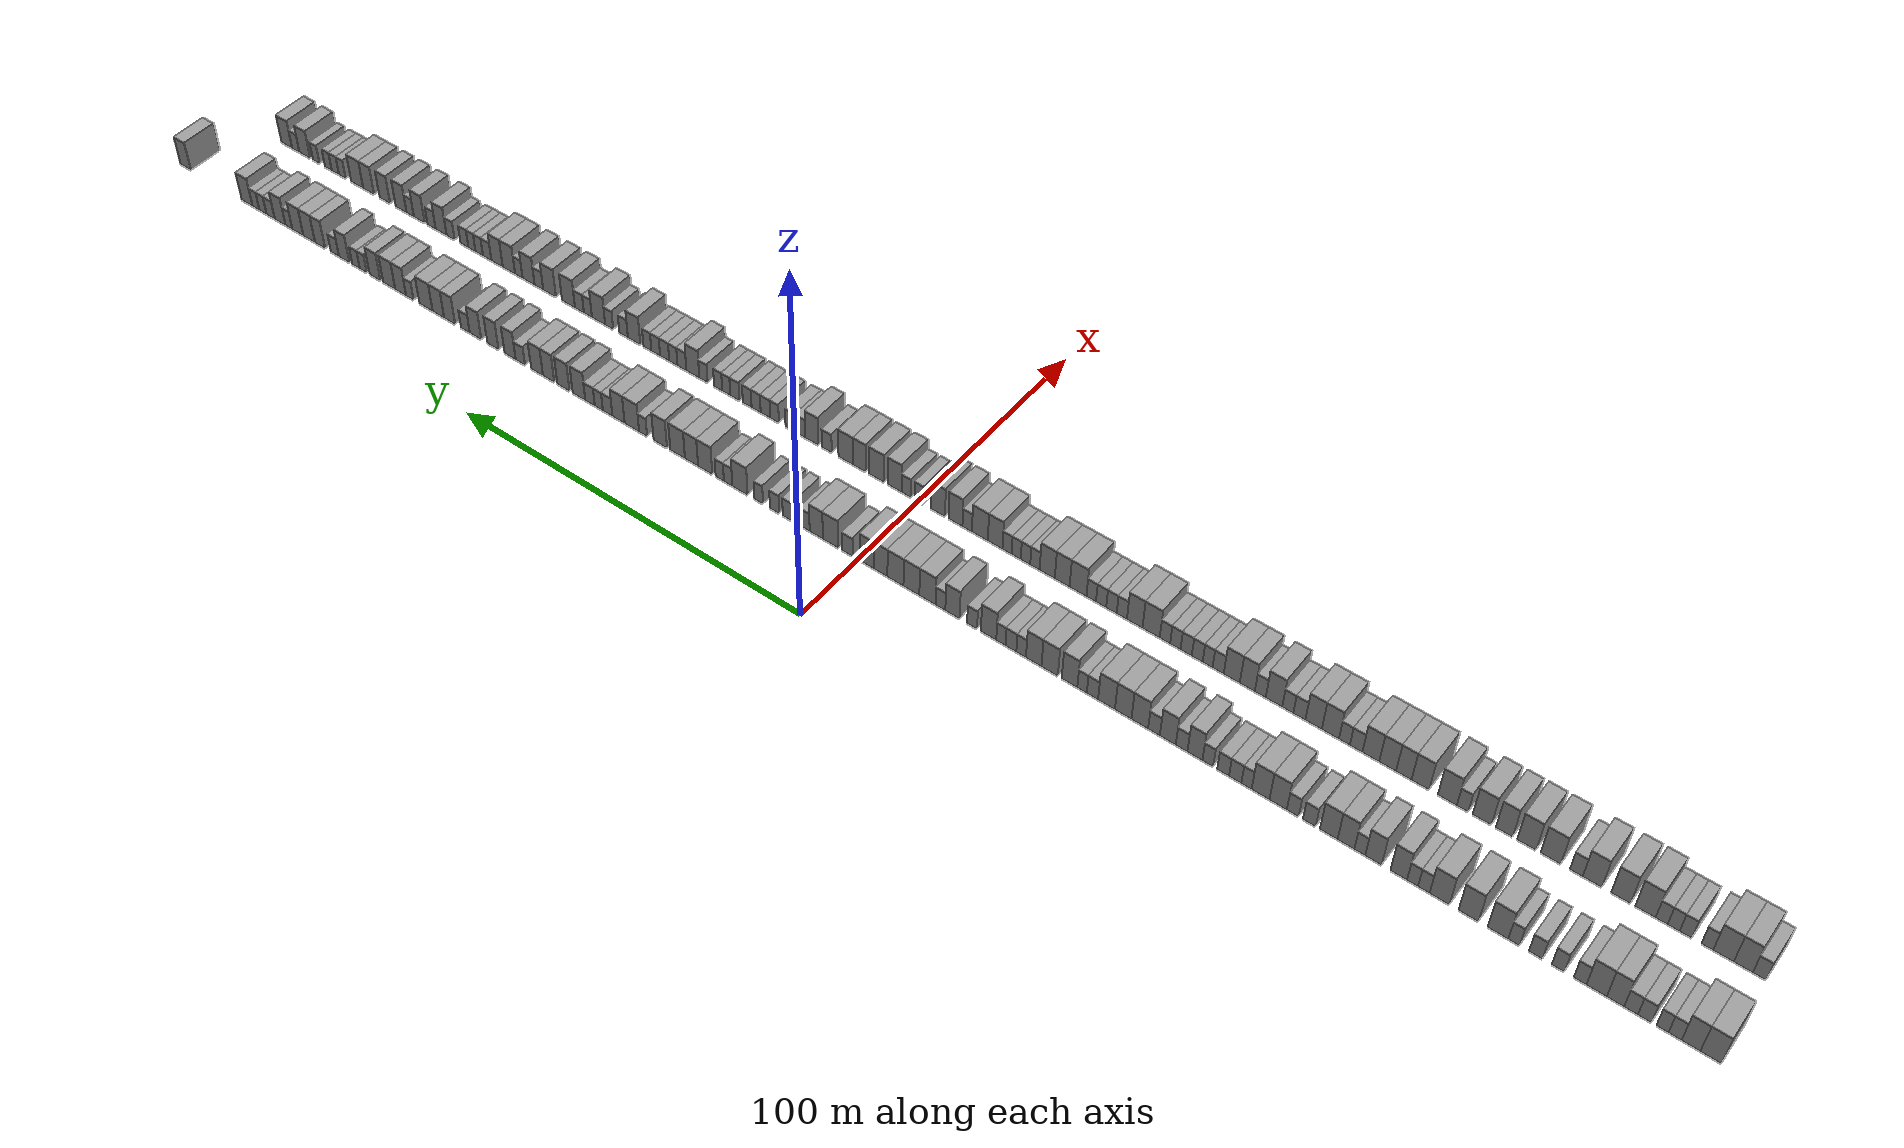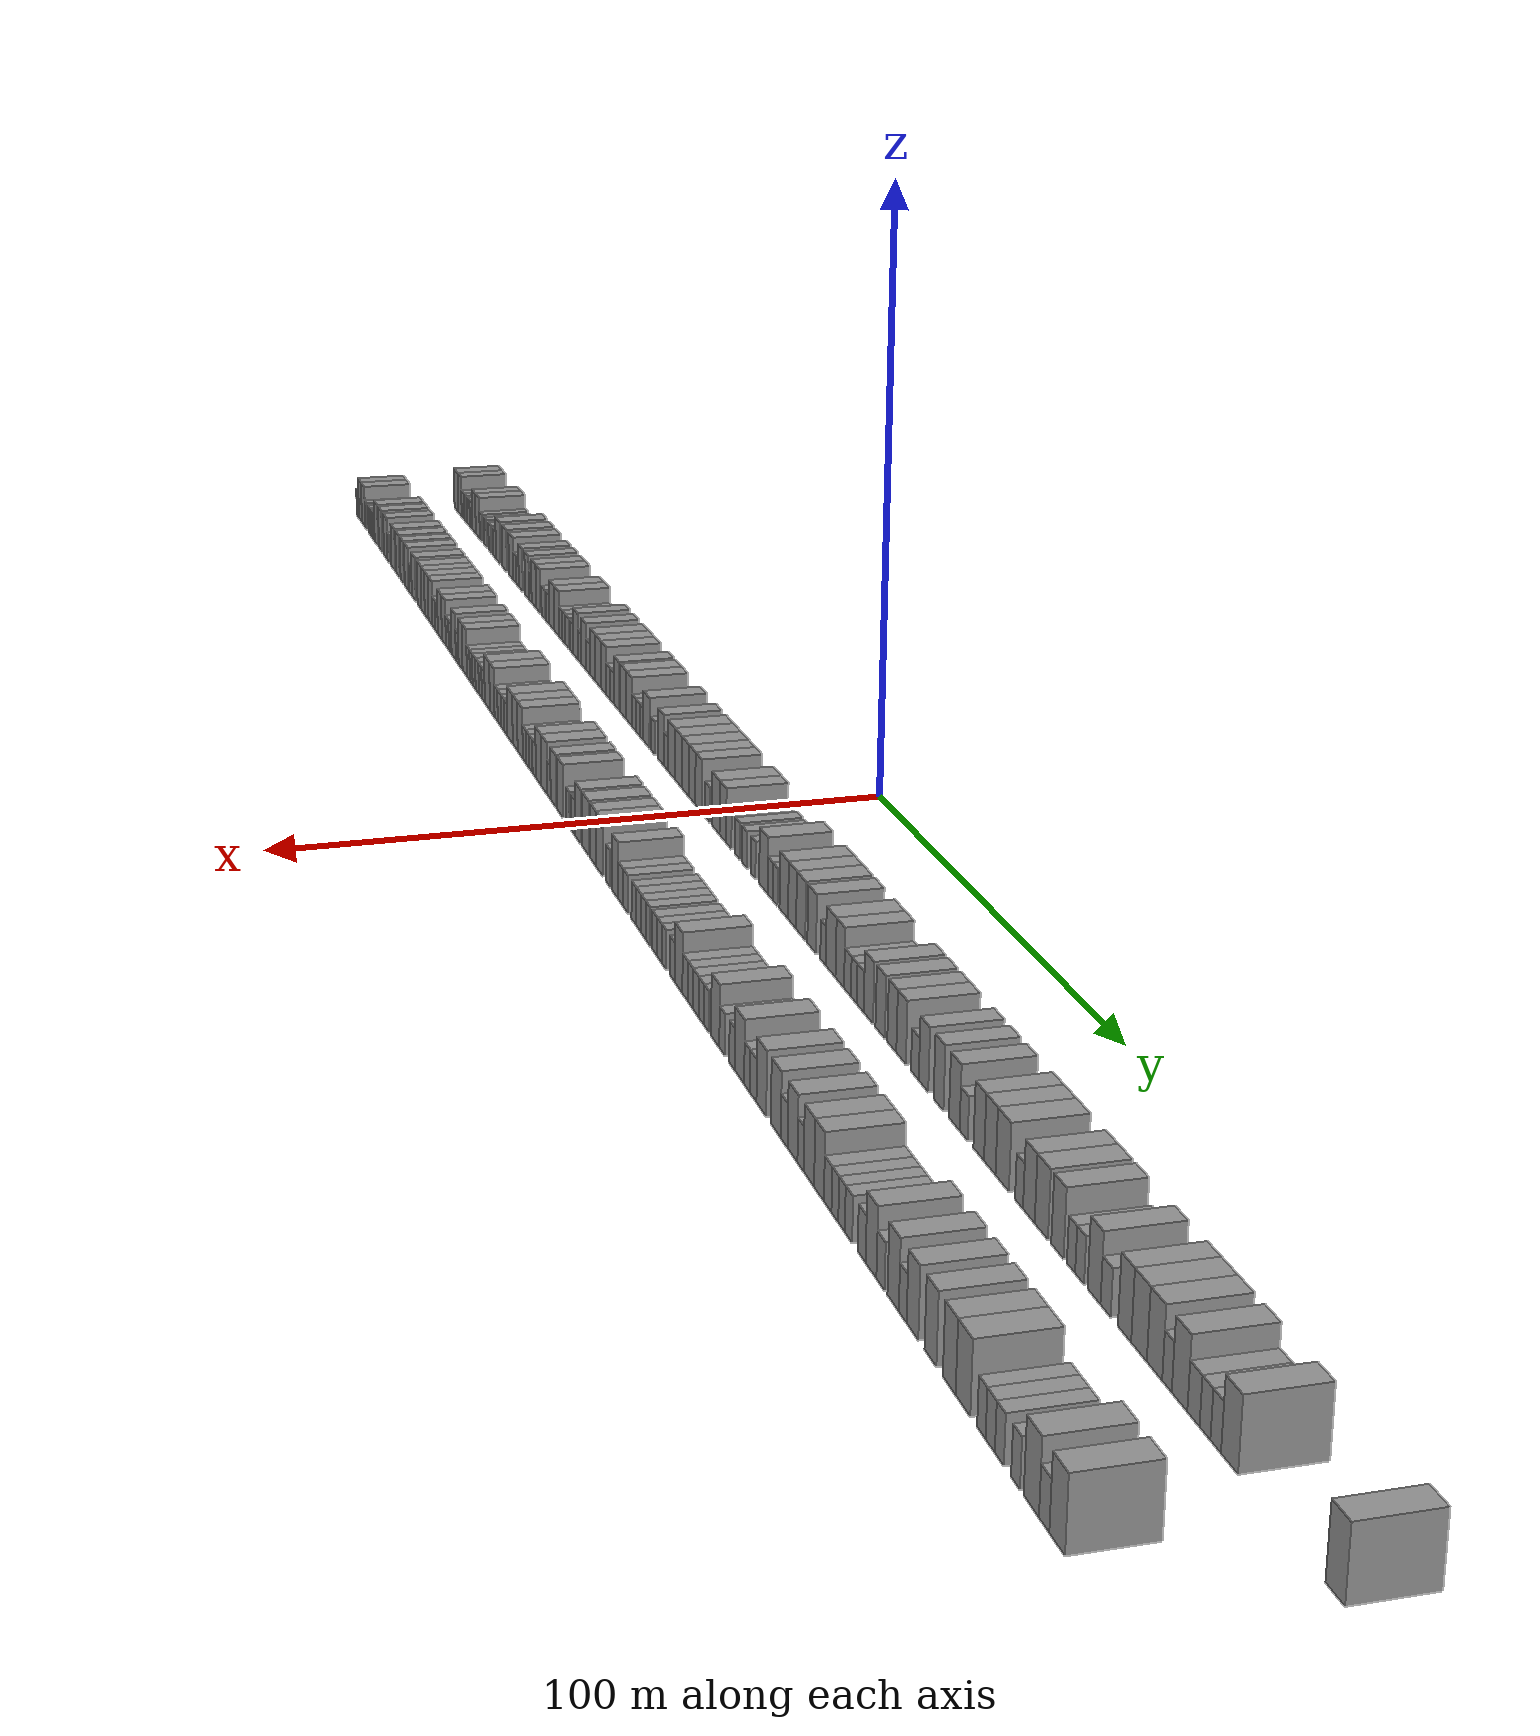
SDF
<sdf version="1.6">
 <world name="default">
  <scene>
   <sky><clouds><speed>12</speed></clouds></sky>
   <ambient>0.4 0.4 0.4 1</ambient>
   <background>0.7 0.7 0.7 1</background>
   <shadows>1</shadows>
  </scene>
  <gravity>0 0 -9.8066</gravity>
  <magnetic_field>6e-06 2.3e-05 -4.2e-05</magnetic_field>
  <physics default="0" name="default_physics" type="ode">
   <ode>
    <solver>
     <type>quick</type>
     <iters>10</iters>
     <sor>1.0</sor>
     <use_dynamic_moi_rescaling>0</use_dynamic_moi_rescaling>
    </solver>
    <constraints>
     <cfm>0</cfm>
     <erp>0.2</erp>
     <contact_max_correcting_vel>100</contact_max_correcting_vel>
     <contact_surface_layer>0.001</contact_surface_layer>
    </constraints>
   </ode>
   <max_step_size>0.004</max_step_size>
   <real_time_factor>1</real_time_factor>
   <real_time_update_rate>250</real_time_update_rate>
  </physics>
  <light name="sun" type="directional">
   <pose>0 0 10 0 0 0</pose>
   <diffuse>0.8 0.8 0.8 1</diffuse>
   <specular>0.2 0.2 0.2 1</specular>
   <attenuation>
    <range>1000</range>
    <constant>0.9</constant>
    <linear>0.01</linear>
    <quadratic>0.001</quadratic>
   </attenuation>
   <direction>-0.5 0.1 -0.9</direction>
  </light>
  <model name="building_1">
   <static>1</static>
   <pose>25.0000 -201.8715 0 0.000000 0.000000 0.000000</pose>
   <link name="link">
    <pose>0 0 4.50 0 0 0</pose>
    <collision name="collision"><geometry><box><size>10.0000 4.2571 9.0000</size></box></geometry></collision>
    <visual name="visual">
     <cast_shadows>0</cast_shadows>
     <geometry><box><size>10.0000 4.2571 9.0000</size></box></geometry>
     <material>
      <script>
       <uri>model://grey_wall/materials/scripts</uri>
       <uri>model://grey_wall/materials/textures</uri>
       <name>vrc/grey_wall</name>
      </script>
     </material>
    </visual>
   </link>
  </model>
  <model name="building_2">
   <static>1</static>
   <pose>25.0000 -197.8458 0 0.000000 0.000000 0.000000</pose>
   <link name="link">
    <pose>0 0 4.50 0 0 0</pose>
    <collision name="collision"><geometry><box><size>10.0000 3.7942 9.0000</size></box></geometry></collision>
    <visual name="visual">
     <cast_shadows>0</cast_shadows>
     <geometry><box><size>10.0000 3.7942 9.0000</size></box></geometry>
     <material>
      <script>
       <uri>model://grey_wall/materials/scripts</uri>
       <uri>model://grey_wall/materials/textures</uri>
       <name>vrc/grey_wall</name>
      </script>
     </material>
    </visual>
   </link>
  </model>
  <model name="building_3">
   <static>1</static>
   <pose>25.0000 -194.6153 0 0.000000 0.000000 0.000000</pose>
   <link name="link">
    <pose>0 0 3.00 0 0 0</pose>
    <collision name="collision"><geometry><box><size>10.0000 2.6668 6.0000</size></box></geometry></collision>
    <visual name="visual">
     <cast_shadows>0</cast_shadows>
     <geometry><box><size>10.0000 2.6668 6.0000</size></box></geometry>
     <material>
      <script>
       <uri>model://grey_wall/materials/scripts</uri>
       <uri>model://grey_wall/materials/textures</uri>
       <name>vrc/grey_wall</name>
      </script>
     </material>
    </visual>
   </link>
  </model>
  <model name="building_4">
   <static>1</static>
   <pose>25.0000 -192.0383 0 0.000000 0.000000 0.000000</pose>
   <link name="link">
    <pose>0 0 3.00 0 0 0</pose>
    <collision name="collision"><geometry><box><size>10.0000 2.4872 6.0000</size></box></geometry></collision>
    <visual name="visual">
     <cast_shadows>0</cast_shadows>
     <geometry><box><size>10.0000 2.4872 6.0000</size></box></geometry>
     <material>
      <script>
       <uri>model://grey_wall/materials/scripts</uri>
       <uri>model://grey_wall/materials/textures</uri>
       <name>vrc/grey_wall</name>
      </script>
     </material>
    </visual>
   </link>
  </model>
  <model name="building_5">
   <static>1</static>
   <pose>25.0000 -188.4017 0 0.000000 0.000000 0.000000</pose>
   <link name="link">
    <pose>0 0 3.00 0 0 0</pose>
    <collision name="collision"><geometry><box><size>10.0000 2.7860 6.0000</size></box></geometry></collision>
    <visual name="visual">
     <cast_shadows>0</cast_shadows>
     <geometry><box><size>10.0000 2.7860 6.0000</size></box></geometry>
     <material>
      <script>
       <uri>model://grey_wall/materials/scripts</uri>
       <uri>model://grey_wall/materials/textures</uri>
       <name>vrc/grey_wall</name>
      </script>
     </material>
    </visual>
   </link>
  </model>
  <model name="building_6">
   <static>1</static>
   <pose>25.0000 -185.5879 0 0.000000 0.000000 0.000000</pose>
   <link name="link">
    <pose>0 0 3.00 0 0 0</pose>
    <collision name="collision"><geometry><box><size>10.0000 2.8416 6.0000</size></box></geometry></collision>
    <visual name="visual">
     <cast_shadows>0</cast_shadows>
     <geometry><box><size>10.0000 2.8416 6.0000</size></box></geometry>
     <material>
      <script>
       <uri>model://grey_wall/materials/scripts</uri>
       <uri>model://grey_wall/materials/textures</uri>
       <name>vrc/grey_wall</name>
      </script>
     </material>
    </visual>
   </link>
  </model>
  <model name="building_7">
   <static>1</static>
   <pose>25.0000 -182.3640 0 0.000000 0.000000 0.000000</pose>
   <link name="link">
    <pose>0 0 4.50 0 0 0</pose>
    <collision name="collision"><geometry><box><size>10.0000 3.6061 9.0000</size></box></geometry></collision>
    <visual name="visual">
     <cast_shadows>0</cast_shadows>
     <geometry><box><size>10.0000 3.6061 9.0000</size></box></geometry>
     <material>
      <script>
       <uri>model://grey_wall/materials/scripts</uri>
       <uri>model://grey_wall/materials/textures</uri>
       <name>vrc/grey_wall</name>
      </script>
     </material>
    </visual>
   </link>
  </model>
  <model name="building_8">
   <static>1</static>
   <pose>25.0000 -178.4295 0 0.000000 0.000000 0.000000</pose>
   <link name="link">
    <pose>0 0 4.50 0 0 0</pose>
    <collision name="collision"><geometry><box><size>10.0000 4.2630 9.0000</size></box></geometry></collision>
    <visual name="visual">
     <cast_shadows>0</cast_shadows>
     <geometry><box><size>10.0000 4.2630 9.0000</size></box></geometry>
     <material>
      <script>
       <uri>model://grey_wall/materials/scripts</uri>
       <uri>model://grey_wall/materials/textures</uri>
       <name>vrc/grey_wall</name>
      </script>
     </material>
    </visual>
   </link>
  </model>
  <model name="building_9">
   <static>1</static>
   <pose>25.0000 -174.9708 0 0.000000 0.000000 0.000000</pose>
   <link name="link">
    <pose>0 0 3.00 0 0 0</pose>
    <collision name="collision"><geometry><box><size>10.0000 2.6544 6.0000</size></box></geometry></collision>
    <visual name="visual">
     <cast_shadows>0</cast_shadows>
     <geometry><box><size>10.0000 2.6544 6.0000</size></box></geometry>
     <material>
      <script>
       <uri>model://grey_wall/materials/scripts</uri>
       <uri>model://grey_wall/materials/textures</uri>
       <name>vrc/grey_wall</name>
      </script>
     </material>
    </visual>
   </link>
  </model>
  <model name="building_10">
   <static>1</static>
   <pose>25.0000 -170.3099 0 0.000000 0.000000 0.000000</pose>
   <link name="link">
    <pose>0 0 3.00 0 0 0</pose>
    <collision name="collision"><geometry><box><size>10.0000 2.6674 6.0000</size></box></geometry></collision>
    <visual name="visual">
     <cast_shadows>0</cast_shadows>
     <geometry><box><size>10.0000 2.6674 6.0000</size></box></geometry>
     <material>
      <script>
       <uri>model://grey_wall/materials/scripts</uri>
       <uri>model://grey_wall/materials/textures</uri>
       <name>vrc/grey_wall</name>
      </script>
     </material>
    </visual>
   </link>
  </model>
  <model name="building_11">
   <static>1</static>
   <pose>25.0000 -165.5331 0 0.000000 0.000000 0.000000</pose>
   <link name="link">
    <pose>0 0 3.00 0 0 0</pose>
    <collision name="collision"><geometry><box><size>10.0000 2.8862 6.0000</size></box></geometry></collision>
    <visual name="visual">
     <cast_shadows>0</cast_shadows>
     <geometry><box><size>10.0000 2.8862 6.0000</size></box></geometry>
     <material>
      <script>
       <uri>model://grey_wall/materials/scripts</uri>
       <uri>model://grey_wall/materials/textures</uri>
       <name>vrc/grey_wall</name>
      </script>
     </material>
    </visual>
   </link>
  </model>
  <model name="building_12">
   <static>1</static>
   <pose>25.0000 -160.8686 0 0.000000 0.000000 0.000000</pose>
   <link name="link">
    <pose>0 0 3.00 0 0 0</pose>
    <collision name="collision"><geometry><box><size>10.0000 2.4428 6.0000</size></box></geometry></collision>
    <visual name="visual">
     <cast_shadows>0</cast_shadows>
     <geometry><box><size>10.0000 2.4428 6.0000</size></box></geometry>
     <material>
      <script>
       <uri>model://grey_wall/materials/scripts</uri>
       <uri>model://grey_wall/materials/textures</uri>
       <name>vrc/grey_wall</name>
      </script>
     </material>
    </visual>
   </link>
  </model>
  <model name="building_13">
   <static>1</static>
   <pose>25.0000 -157.4011 0 0.000000 0.000000 0.000000</pose>
   <link name="link">
    <pose>0 0 4.50 0 0 0</pose>
    <collision name="collision"><geometry><box><size>10.0000 4.4920 9.0000</size></box></geometry></collision>
    <visual name="visual">
     <cast_shadows>0</cast_shadows>
     <geometry><box><size>10.0000 4.4920 9.0000</size></box></geometry>
     <material>
      <script>
       <uri>model://grey_wall/materials/scripts</uri>
       <uri>model://grey_wall/materials/textures</uri>
       <name>vrc/grey_wall</name>
      </script>
     </material>
    </visual>
   </link>
  </model>
  <model name="building_14">
   <static>1</static>
   <pose>25.0000 -150.9676 0 0.000000 0.000000 0.000000</pose>
   <link name="link">
    <pose>0 0 4.50 0 0 0</pose>
    <collision name="collision"><geometry><box><size>10.0000 4.3750 9.0000</size></box></geometry></collision>
    <visual name="visual">
     <cast_shadows>0</cast_shadows>
     <geometry><box><size>10.0000 4.3750 9.0000</size></box></geometry>
     <material>
      <script>
       <uri>model://grey_wall/materials/scripts</uri>
       <uri>model://grey_wall/materials/textures</uri>
       <name>vrc/grey_wall</name>
      </script>
     </material>
    </visual>
   </link>
  </model>
  <model name="building_15">
   <static>1</static>
   <pose>25.0000 -144.5749 0 0.000000 0.000000 0.000000</pose>
   <link name="link">
    <pose>0 0 4.50 0 0 0</pose>
    <collision name="collision"><geometry><box><size>10.0000 4.4104 9.0000</size></box></geometry></collision>
    <visual name="visual">
     <cast_shadows>0</cast_shadows>
     <geometry><box><size>10.0000 4.4104 9.0000</size></box></geometry>
     <material>
      <script>
       <uri>model://grey_wall/materials/scripts</uri>
       <uri>model://grey_wall/materials/textures</uri>
       <name>vrc/grey_wall</name>
      </script>
     </material>
    </visual>
   </link>
  </model>
  <model name="building_16">
   <static>1</static>
   <pose>25.0000 -141.0750 0 0.000000 0.000000 0.000000</pose>
   <link name="link">
    <pose>0 0 3.00 0 0 0</pose>
    <collision name="collision"><geometry><box><size>10.0000 2.5892 6.0000</size></box></geometry></collision>
    <visual name="visual">
     <cast_shadows>0</cast_shadows>
     <geometry><box><size>10.0000 2.5892 6.0000</size></box></geometry>
     <material>
      <script>
       <uri>model://grey_wall/materials/scripts</uri>
       <uri>model://grey_wall/materials/textures</uri>
       <name>vrc/grey_wall</name>
      </script>
     </material>
    </visual>
   </link>
  </model>
  <model name="building_17">
   <static>1</static>
   <pose>25.0000 -138.5520 0 0.000000 0.000000 0.000000</pose>
   <link name="link">
    <pose>0 0 3.00 0 0 0</pose>
    <collision name="collision"><geometry><box><size>10.0000 2.4569 6.0000</size></box></geometry></collision>
    <visual name="visual">
     <cast_shadows>0</cast_shadows>
     <geometry><box><size>10.0000 2.4569 6.0000</size></box></geometry>
     <material>
      <script>
       <uri>model://grey_wall/materials/scripts</uri>
       <uri>model://grey_wall/materials/textures</uri>
       <name>vrc/grey_wall</name>
      </script>
     </material>
    </visual>
   </link>
  </model>
  <model name="building_18">
   <static>1</static>
   <pose>25.0000 -135.4540 0 0.000000 0.000000 0.000000</pose>
   <link name="link">
    <pose>0 0 4.50 0 0 0</pose>
    <collision name="collision"><geometry><box><size>10.0000 3.7391 9.0000</size></box></geometry></collision>
    <visual name="visual">
     <cast_shadows>0</cast_shadows>
     <geometry><box><size>10.0000 3.7391 9.0000</size></box></geometry>
     <material>
      <script>
       <uri>model://grey_wall/materials/scripts</uri>
       <uri>model://grey_wall/materials/textures</uri>
       <name>vrc/grey_wall</name>
      </script>
     </material>
    </visual>
   </link>
  </model>
  <model name="building_19">
   <static>1</static>
   <pose>25.0000 -129.7280 0 0.000000 0.000000 0.000000</pose>
   <link name="link">
    <pose>0 0 4.50 0 0 0</pose>
    <collision name="collision"><geometry><box><size>10.0000 3.7128 9.0000</size></box></geometry></collision>
    <visual name="visual">
     <cast_shadows>0</cast_shadows>
     <geometry><box><size>10.0000 3.7128 9.0000</size></box></geometry>
     <material>
      <script>
       <uri>model://grey_wall/materials/scripts</uri>
       <uri>model://grey_wall/materials/textures</uri>
       <name>vrc/grey_wall</name>
      </script>
     </material>
    </visual>
   </link>
  </model>
  <model name="building_20">
   <static>1</static>
   <pose>25.0000 -126.6309 0 0.000000 0.000000 0.000000</pose>
   <link name="link">
    <pose>0 0 3.00 0 0 0</pose>
    <collision name="collision"><geometry><box><size>10.0000 2.4814 6.0000</size></box></geometry></collision>
    <visual name="visual">
     <cast_shadows>0</cast_shadows>
     <geometry><box><size>10.0000 2.4814 6.0000</size></box></geometry>
     <material>
      <script>
       <uri>model://grey_wall/materials/scripts</uri>
       <uri>model://grey_wall/materials/textures</uri>
       <name>vrc/grey_wall</name>
      </script>
     </material>
    </visual>
   </link>
  </model>
  <model name="building_21">
   <static>1</static>
   <pose>25.0000 -123.4586 0 0.000000 0.000000 0.000000</pose>
   <link name="link">
    <pose>0 0 4.50 0 0 0</pose>
    <collision name="collision"><geometry><box><size>10.0000 3.8633 9.0000</size></box></geometry></collision>
    <visual name="visual">
     <cast_shadows>0</cast_shadows>
     <geometry><box><size>10.0000 3.8633 9.0000</size></box></geometry>
     <material>
      <script>
       <uri>model://grey_wall/materials/scripts</uri>
       <uri>model://grey_wall/materials/textures</uri>
       <name>vrc/grey_wall</name>
      </script>
     </material>
    </visual>
   </link>
  </model>
  <model name="building_22">
   <static>1</static>
   <pose>25.0000 -119.4799 0 0.000000 0.000000 0.000000</pose>
   <link name="link">
    <pose>0 0 4.50 0 0 0</pose>
    <collision name="collision"><geometry><box><size>10.0000 4.0941 9.0000</size></box></geometry></collision>
    <visual name="visual">
     <cast_shadows>0</cast_shadows>
     <geometry><box><size>10.0000 4.0941 9.0000</size></box></geometry>
     <material>
      <script>
       <uri>model://grey_wall/materials/scripts</uri>
       <uri>model://grey_wall/materials/textures</uri>
       <name>vrc/grey_wall</name>
      </script>
     </material>
    </visual>
   </link>
  </model>
  <model name="building_23">
   <static>1</static>
   <pose>25.0000 -114.9615 0 0.000000 0.000000 0.000000</pose>
   <link name="link">
    <pose>0 0 3.00 0 0 0</pose>
    <collision name="collision"><geometry><box><size>10.0000 2.9427 6.0000</size></box></geometry></collision>
    <visual name="visual">
     <cast_shadows>0</cast_shadows>
     <geometry><box><size>10.0000 2.9427 6.0000</size></box></geometry>
     <material>
      <script>
       <uri>model://grey_wall/materials/scripts</uri>
       <uri>model://grey_wall/materials/textures</uri>
       <name>vrc/grey_wall</name>
      </script>
     </material>
    </visual>
   </link>
  </model>
  <model name="building_24">
   <static>1</static>
   <pose>25.0000 -111.1020 0 0.000000 0.000000 0.000000</pose>
   <link name="link">
    <pose>0 0 3.00 0 0 0</pose>
    <collision name="collision"><geometry><box><size>10.0000 2.7763 6.0000</size></box></geometry></collision>
    <visual name="visual">
     <cast_shadows>0</cast_shadows>
     <geometry><box><size>10.0000 2.7763 6.0000</size></box></geometry>
     <material>
      <script>
       <uri>model://grey_wall/materials/scripts</uri>
       <uri>model://grey_wall/materials/textures</uri>
       <name>vrc/grey_wall</name>
      </script>
     </material>
    </visual>
   </link>
  </model>
  <model name="building_25">
   <static>1</static>
   <pose>25.0000 -107.6616 0 0.000000 0.000000 0.000000</pose>
   <link name="link">
    <pose>0 0 4.50 0 0 0</pose>
    <collision name="collision"><geometry><box><size>10.0000 4.1044 9.0000</size></box></geometry></collision>
    <visual name="visual">
     <cast_shadows>0</cast_shadows>
     <geometry><box><size>10.0000 4.1044 9.0000</size></box></geometry>
     <material>
      <script>
       <uri>model://grey_wall/materials/scripts</uri>
       <uri>model://grey_wall/materials/textures</uri>
       <name>vrc/grey_wall</name>
      </script>
     </material>
    </visual>
   </link>
  </model>
  <model name="building_26">
   <static>1</static>
   <pose>25.0000 -103.4904 0 0.000000 0.000000 0.000000</pose>
   <link name="link">
    <pose>0 0 4.50 0 0 0</pose>
    <collision name="collision"><geometry><box><size>10.0000 4.2381 9.0000</size></box></geometry></collision>
    <visual name="visual">
     <cast_shadows>0</cast_shadows>
     <geometry><box><size>10.0000 4.2381 9.0000</size></box></geometry>
     <material>
      <script>
       <uri>model://grey_wall/materials/scripts</uri>
       <uri>model://grey_wall/materials/textures</uri>
       <name>vrc/grey_wall</name>
      </script>
     </material>
    </visual>
   </link>
  </model>
  <model name="building_27">
   <static>1</static>
   <pose>25.0000 -100.1394 0 0.000000 0.000000 0.000000</pose>
   <link name="link">
    <pose>0 0 3.00 0 0 0</pose>
    <collision name="collision"><geometry><box><size>10.0000 2.4638 6.0000</size></box></geometry></collision>
    <visual name="visual">
     <cast_shadows>0</cast_shadows>
     <geometry><box><size>10.0000 2.4638 6.0000</size></box></geometry>
     <material>
      <script>
       <uri>model://grey_wall/materials/scripts</uri>
       <uri>model://grey_wall/materials/textures</uri>
       <name>vrc/grey_wall</name>
      </script>
     </material>
    </visual>
   </link>
  </model>
  <model name="building_28">
   <static>1</static>
   <pose>25.0000 -97.4309 0 0.000000 0.000000 0.000000</pose>
   <link name="link">
    <pose>0 0 3.00 0 0 0</pose>
    <collision name="collision"><geometry><box><size>10.0000 2.9532 6.0000</size></box></geometry></collision>
    <visual name="visual">
     <cast_shadows>0</cast_shadows>
     <geometry><box><size>10.0000 2.9532 6.0000</size></box></geometry>
     <material>
      <script>
       <uri>model://grey_wall/materials/scripts</uri>
       <uri>model://grey_wall/materials/textures</uri>
       <name>vrc/grey_wall</name>
      </script>
     </material>
    </visual>
   </link>
  </model>
  <model name="building_29">
   <static>1</static>
   <pose>25.0000 -94.5324 0 0.000000 0.000000 0.000000</pose>
   <link name="link">
    <pose>0 0 3.00 0 0 0</pose>
    <collision name="collision"><geometry><box><size>10.0000 2.8439 6.0000</size></box></geometry></collision>
    <visual name="visual">
     <cast_shadows>0</cast_shadows>
     <geometry><box><size>10.0000 2.8439 6.0000</size></box></geometry>
     <material>
      <script>
       <uri>model://grey_wall/materials/scripts</uri>
       <uri>model://grey_wall/materials/textures</uri>
       <name>vrc/grey_wall</name>
      </script>
     </material>
    </visual>
   </link>
  </model>
  <model name="building_30">
   <static>1</static>
   <pose>25.0000 -90.8245 0 0.000000 0.000000 0.000000</pose>
   <link name="link">
    <pose>0 0 3.00 0 0 0</pose>
    <collision name="collision"><geometry><box><size>10.0000 2.5719 6.0000</size></box></geometry></collision>
    <visual name="visual">
     <cast_shadows>0</cast_shadows>
     <geometry><box><size>10.0000 2.5719 6.0000</size></box></geometry>
     <material>
      <script>
       <uri>model://grey_wall/materials/scripts</uri>
       <uri>model://grey_wall/materials/textures</uri>
       <name>vrc/grey_wall</name>
      </script>
     </material>
    </visual>
   </link>
  </model>
  <model name="building_31">
   <static>1</static>
   <pose>25.0000 -87.6976 0 0.000000 0.000000 0.000000</pose>
   <link name="link">
    <pose>0 0 4.50 0 0 0</pose>
    <collision name="collision"><geometry><box><size>10.0000 3.6820 9.0000</size></box></geometry></collision>
    <visual name="visual">
     <cast_shadows>0</cast_shadows>
     <geometry><box><size>10.0000 3.6820 9.0000</size></box></geometry>
     <material>
      <script>
       <uri>model://grey_wall/materials/scripts</uri>
       <uri>model://grey_wall/materials/textures</uri>
       <name>vrc/grey_wall</name>
      </script>
     </material>
    </visual>
   </link>
  </model>
  <model name="building_32">
   <static>1</static>
   <pose>25.0000 -84.4292 0 0.000000 0.000000 0.000000</pose>
   <link name="link">
    <pose>0 0 3.00 0 0 0</pose>
    <collision name="collision"><geometry><box><size>10.0000 2.8549 6.0000</size></box></geometry></collision>
    <visual name="visual">
     <cast_shadows>0</cast_shadows>
     <geometry><box><size>10.0000 2.8549 6.0000</size></box></geometry>
     <material>
      <script>
       <uri>model://grey_wall/materials/scripts</uri>
       <uri>model://grey_wall/materials/textures</uri>
       <name>vrc/grey_wall</name>
      </script>
     </material>
    </visual>
   </link>
  </model>
  <model name="building_33">
   <static>1</static>
   <pose>25.0000 -81.0458 0 0.000000 0.000000 0.000000</pose>
   <link name="link">
    <pose>0 0 4.50 0 0 0</pose>
    <collision name="collision"><geometry><box><size>10.0000 3.9118 9.0000</size></box></geometry></collision>
    <visual name="visual">
     <cast_shadows>0</cast_shadows>
     <geometry><box><size>10.0000 3.9118 9.0000</size></box></geometry>
     <material>
      <script>
       <uri>model://grey_wall/materials/scripts</uri>
       <uri>model://grey_wall/materials/textures</uri>
       <name>vrc/grey_wall</name>
      </script>
     </material>
    </visual>
   </link>
  </model>
  <model name="building_34">
   <static>1</static>
   <pose>25.0000 -77.6416 0 0.000000 0.000000 0.000000</pose>
   <link name="link">
    <pose>0 0 3.00 0 0 0</pose>
    <collision name="collision"><geometry><box><size>10.0000 2.8966 6.0000</size></box></geometry></collision>
    <visual name="visual">
     <cast_shadows>0</cast_shadows>
     <geometry><box><size>10.0000 2.8966 6.0000</size></box></geometry>
     <material>
      <script>
       <uri>model://grey_wall/materials/scripts</uri>
       <uri>model://grey_wall/materials/textures</uri>
       <name>vrc/grey_wall</name>
      </script>
     </material>
    </visual>
   </link>
  </model>
  <model name="building_35">
   <static>1</static>
   <pose>25.0000 -74.1126 0 0.000000 0.000000 0.000000</pose>
   <link name="link">
    <pose>0 0 4.50 0 0 0</pose>
    <collision name="collision"><geometry><box><size>10.0000 4.1612 9.0000</size></box></geometry></collision>
    <visual name="visual">
     <cast_shadows>0</cast_shadows>
     <geometry><box><size>10.0000 4.1612 9.0000</size></box></geometry>
     <material>
      <script>
       <uri>model://grey_wall/materials/scripts</uri>
       <uri>model://grey_wall/materials/textures</uri>
       <name>vrc/grey_wall</name>
      </script>
     </material>
    </visual>
   </link>
  </model>
  <model name="building_36">
   <static>1</static>
   <pose>25.0000 -69.9689 0 0.000000 0.000000 0.000000</pose>
   <link name="link">
    <pose>0 0 4.50 0 0 0</pose>
    <collision name="collision"><geometry><box><size>10.0000 4.1262 9.0000</size></box></geometry></collision>
    <visual name="visual">
     <cast_shadows>0</cast_shadows>
     <geometry><box><size>10.0000 4.1262 9.0000</size></box></geometry>
     <material>
      <script>
       <uri>model://grey_wall/materials/scripts</uri>
       <uri>model://grey_wall/materials/textures</uri>
       <name>vrc/grey_wall</name>
      </script>
     </material>
    </visual>
   </link>
  </model>
  <model name="building_37">
   <static>1</static>
   <pose>25.0000 -65.7747 0 0.000000 0.000000 0.000000</pose>
   <link name="link">
    <pose>0 0 4.50 0 0 0</pose>
    <collision name="collision"><geometry><box><size>10.0000 4.2623 9.0000</size></box></geometry></collision>
    <visual name="visual">
     <cast_shadows>0</cast_shadows>
     <geometry><box><size>10.0000 4.2623 9.0000</size></box></geometry>
     <material>
      <script>
       <uri>model://grey_wall/materials/scripts</uri>
       <uri>model://grey_wall/materials/textures</uri>
       <name>vrc/grey_wall</name>
      </script>
     </material>
    </visual>
   </link>
  </model>
  <model name="building_38">
   <static>1</static>
   <pose>25.0000 -62.2208 0 0.000000 0.000000 0.000000</pose>
   <link name="link">
    <pose>0 0 3.00 0 0 0</pose>
    <collision name="collision"><geometry><box><size>10.0000 2.8455 6.0000</size></box></geometry></collision>
    <visual name="visual">
     <cast_shadows>0</cast_shadows>
     <geometry><box><size>10.0000 2.8455 6.0000</size></box></geometry>
     <material>
      <script>
       <uri>model://grey_wall/materials/scripts</uri>
       <uri>model://grey_wall/materials/textures</uri>
       <name>vrc/grey_wall</name>
      </script>
     </material>
    </visual>
   </link>
  </model>
  <model name="building_39">
   <static>1</static>
   <pose>25.0000 -59.5873 0 0.000000 0.000000 0.000000</pose>
   <link name="link">
    <pose>0 0 3.00 0 0 0</pose>
    <collision name="collision"><geometry><box><size>10.0000 2.4215 6.0000</size></box></geometry></collision>
    <visual name="visual">
     <cast_shadows>0</cast_shadows>
     <geometry><box><size>10.0000 2.4215 6.0000</size></box></geometry>
     <material>
      <script>
       <uri>model://grey_wall/materials/scripts</uri>
       <uri>model://grey_wall/materials/textures</uri>
       <name>vrc/grey_wall</name>
      </script>
     </material>
    </visual>
   </link>
  </model>
  <model name="building_40">
   <static>1</static>
   <pose>25.0000 -56.3808 0 0.000000 0.000000 0.000000</pose>
   <link name="link">
    <pose>0 0 4.50 0 0 0</pose>
    <collision name="collision"><geometry><box><size>10.0000 3.9916 9.0000</size></box></geometry></collision>
    <visual name="visual">
     <cast_shadows>0</cast_shadows>
     <geometry><box><size>10.0000 3.9916 9.0000</size></box></geometry>
     <material>
      <script>
       <uri>model://grey_wall/materials/scripts</uri>
       <uri>model://grey_wall/materials/textures</uri>
       <name>vrc/grey_wall</name>
      </script>
     </material>
    </visual>
   </link>
  </model>
  <model name="building_41">
   <static>1</static>
   <pose>25.0000 -51.2658 0 0.000000 0.000000 0.000000</pose>
   <link name="link">
    <pose>0 0 4.50 0 0 0</pose>
    <collision name="collision"><geometry><box><size>10.0000 4.2384 9.0000</size></box></geometry></collision>
    <visual name="visual">
     <cast_shadows>0</cast_shadows>
     <geometry><box><size>10.0000 4.2384 9.0000</size></box></geometry>
     <material>
      <script>
       <uri>model://grey_wall/materials/scripts</uri>
       <uri>model://grey_wall/materials/textures</uri>
       <name>vrc/grey_wall</name>
      </script>
     </material>
    </visual>
   </link>
  </model>
  <model name="building_42">
   <static>1</static>
   <pose>25.0000 -47.1261 0 0.000000 0.000000 0.000000</pose>
   <link name="link">
    <pose>0 0 4.50 0 0 0</pose>
    <collision name="collision"><geometry><box><size>10.0000 4.0411 9.0000</size></box></geometry></collision>
    <visual name="visual">
     <cast_shadows>0</cast_shadows>
     <geometry><box><size>10.0000 4.0411 9.0000</size></box></geometry>
     <material>
      <script>
       <uri>model://grey_wall/materials/scripts</uri>
       <uri>model://grey_wall/materials/textures</uri>
       <name>vrc/grey_wall</name>
      </script>
     </material>
    </visual>
   </link>
  </model>
  <model name="building_43">
   <static>1</static>
   <pose>25.0000 -43.8593 0 0.000000 0.000000 0.000000</pose>
   <link name="link">
    <pose>0 0 3.00 0 0 0</pose>
    <collision name="collision"><geometry><box><size>10.0000 2.4925 6.0000</size></box></geometry></collision>
    <visual name="visual">
     <cast_shadows>0</cast_shadows>
     <geometry><box><size>10.0000 2.4925 6.0000</size></box></geometry>
     <material>
      <script>
       <uri>model://grey_wall/materials/scripts</uri>
       <uri>model://grey_wall/materials/textures</uri>
       <name>vrc/grey_wall</name>
      </script>
     </material>
    </visual>
   </link>
  </model>
  <model name="building_44">
   <static>1</static>
   <pose>25.0000 -41.1967 0 0.000000 0.000000 0.000000</pose>
   <link name="link">
    <pose>0 0 3.00 0 0 0</pose>
    <collision name="collision"><geometry><box><size>10.0000 2.8325 6.0000</size></box></geometry></collision>
    <visual name="visual">
     <cast_shadows>0</cast_shadows>
     <geometry><box><size>10.0000 2.8325 6.0000</size></box></geometry>
     <material>
      <script>
       <uri>model://grey_wall/materials/scripts</uri>
       <uri>model://grey_wall/materials/textures</uri>
       <name>vrc/grey_wall</name>
      </script>
     </material>
    </visual>
   </link>
  </model>
  <model name="building_45">
   <static>1</static>
   <pose>25.0000 -38.5544 0 0.000000 0.000000 0.000000</pose>
   <link name="link">
    <pose>0 0 3.00 0 0 0</pose>
    <collision name="collision"><geometry><box><size>10.0000 2.4520 6.0000</size></box></geometry></collision>
    <visual name="visual">
     <cast_shadows>0</cast_shadows>
     <geometry><box><size>10.0000 2.4520 6.0000</size></box></geometry>
     <material>
      <script>
       <uri>model://grey_wall/materials/scripts</uri>
       <uri>model://grey_wall/materials/textures</uri>
       <name>vrc/grey_wall</name>
      </script>
     </material>
    </visual>
   </link>
  </model>
  <model name="building_46">
   <static>1</static>
   <pose>25.0000 -35.2823 0 0.000000 0.000000 0.000000</pose>
   <link name="link">
    <pose>0 0 4.50 0 0 0</pose>
    <collision name="collision"><geometry><box><size>10.0000 4.0922 9.0000</size></box></geometry></collision>
    <visual name="visual">
     <cast_shadows>0</cast_shadows>
     <geometry><box><size>10.0000 4.0922 9.0000</size></box></geometry>
     <material>
      <script>
       <uri>model://grey_wall/materials/scripts</uri>
       <uri>model://grey_wall/materials/textures</uri>
       <name>vrc/grey_wall</name>
      </script>
     </material>
    </visual>
   </link>
  </model>
  <model name="building_47">
   <static>1</static>
   <pose>25.0000 -30.9159 0 0.000000 0.000000 0.000000</pose>
   <link name="link">
    <pose>0 0 3.00 0 0 0</pose>
    <collision name="collision"><geometry><box><size>10.0000 2.6406 6.0000</size></box></geometry></collision>
    <visual name="visual">
     <cast_shadows>0</cast_shadows>
     <geometry><box><size>10.0000 2.6406 6.0000</size></box></geometry>
     <material>
      <script>
       <uri>model://grey_wall/materials/scripts</uri>
       <uri>model://grey_wall/materials/textures</uri>
       <name>vrc/grey_wall</name>
      </script>
     </material>
    </visual>
   </link>
  </model>
  <model name="building_48">
   <static>1</static>
   <pose>25.0000 -25.6703 0 0.000000 0.000000 0.000000</pose>
   <link name="link">
    <pose>0 0 4.50 0 0 0</pose>
    <collision name="collision"><geometry><box><size>10.0000 3.8506 9.0000</size></box></geometry></collision>
    <visual name="visual">
     <cast_shadows>0</cast_shadows>
     <geometry><box><size>10.0000 3.8506 9.0000</size></box></geometry>
     <material>
      <script>
       <uri>model://grey_wall/materials/scripts</uri>
       <uri>model://grey_wall/materials/textures</uri>
       <name>vrc/grey_wall</name>
      </script>
     </material>
    </visual>
   </link>
  </model>
  <model name="building_49">
   <static>1</static>
   <pose>25.0000 -22.4539 0 0.000000 0.000000 0.000000</pose>
   <link name="link">
    <pose>0 0 3.00 0 0 0</pose>
    <collision name="collision"><geometry><box><size>10.0000 2.5822 6.0000</size></box></geometry></collision>
    <visual name="visual">
     <cast_shadows>0</cast_shadows>
     <geometry><box><size>10.0000 2.5822 6.0000</size></box></geometry>
     <material>
      <script>
       <uri>model://grey_wall/materials/scripts</uri>
       <uri>model://grey_wall/materials/textures</uri>
       <name>vrc/grey_wall</name>
      </script>
     </material>
    </visual>
   </link>
  </model>
  <model name="building_50">
   <static>1</static>
   <pose>25.0000 -18.9364 0 0.000000 0.000000 0.000000</pose>
   <link name="link">
    <pose>0 0 4.50 0 0 0</pose>
    <collision name="collision"><geometry><box><size>10.0000 4.4528 9.0000</size></box></geometry></collision>
    <visual name="visual">
     <cast_shadows>0</cast_shadows>
     <geometry><box><size>10.0000 4.4528 9.0000</size></box></geometry>
     <material>
      <script>
       <uri>model://grey_wall/materials/scripts</uri>
       <uri>model://grey_wall/materials/textures</uri>
       <name>vrc/grey_wall</name>
      </script>
     </material>
    </visual>
   </link>
  </model>
  <model name="building_51">
   <static>1</static>
   <pose>25.0000 -14.5381 0 0.000000 0.000000 0.000000</pose>
   <link name="link">
    <pose>0 0 4.50 0 0 0</pose>
    <collision name="collision"><geometry><box><size>10.0000 4.3439 9.0000</size></box></geometry></collision>
    <visual name="visual">
     <cast_shadows>0</cast_shadows>
     <geometry><box><size>10.0000 4.3439 9.0000</size></box></geometry>
     <material>
      <script>
       <uri>model://grey_wall/materials/scripts</uri>
       <uri>model://grey_wall/materials/textures</uri>
       <name>vrc/grey_wall</name>
      </script>
     </material>
    </visual>
   </link>
  </model>
  <model name="building_52">
   <static>1</static>
   <pose>25.0000 -10.1590 0 0.000000 0.000000 0.000000</pose>
   <link name="link">
    <pose>0 0 4.50 0 0 0</pose>
    <collision name="collision"><geometry><box><size>10.0000 4.4143 9.0000</size></box></geometry></collision>
    <visual name="visual">
     <cast_shadows>0</cast_shadows>
     <geometry><box><size>10.0000 4.4143 9.0000</size></box></geometry>
     <material>
      <script>
       <uri>model://grey_wall/materials/scripts</uri>
       <uri>model://grey_wall/materials/textures</uri>
       <name>vrc/grey_wall</name>
      </script>
     </material>
    </visual>
   </link>
  </model>
  <model name="building_53">
   <static>1</static>
   <pose>25.0000 -6.0237 0 0.000000 0.000000 0.000000</pose>
   <link name="link">
    <pose>0 0 4.50 0 0 0</pose>
    <collision name="collision"><geometry><box><size>10.0000 3.8564 9.0000</size></box></geometry></collision>
    <visual name="visual">
     <cast_shadows>0</cast_shadows>
     <geometry><box><size>10.0000 3.8564 9.0000</size></box></geometry>
     <material>
      <script>
       <uri>model://grey_wall/materials/scripts</uri>
       <uri>model://grey_wall/materials/textures</uri>
       <name>vrc/grey_wall</name>
      </script>
     </material>
    </visual>
   </link>
  </model>
  <model name="building_54">
   <static>1</static>
   <pose>25.0000 -2.1861 0 0.000000 0.000000 0.000000</pose>
   <link name="link">
    <pose>0 0 4.50 0 0 0</pose>
    <collision name="collision"><geometry><box><size>10.0000 3.8187 9.0000</size></box></geometry></collision>
    <visual name="visual">
     <cast_shadows>0</cast_shadows>
     <geometry><box><size>10.0000 3.8187 9.0000</size></box></geometry>
     <material>
      <script>
       <uri>model://grey_wall/materials/scripts</uri>
       <uri>model://grey_wall/materials/textures</uri>
       <name>vrc/grey_wall</name>
      </script>
     </material>
    </visual>
   </link>
  </model>
  <model name="building_55">
   <static>1</static>
   <pose>25.0000 3.2048 0 0.000000 0.000000 0.000000</pose>
   <link name="link">
    <pose>0 0 3.00 0 0 0</pose>
    <collision name="collision"><geometry><box><size>10.0000 2.9631 6.0000</size></box></geometry></collision>
    <visual name="visual">
     <cast_shadows>0</cast_shadows>
     <geometry><box><size>10.0000 2.9631 6.0000</size></box></geometry>
     <material>
      <script>
       <uri>model://grey_wall/materials/scripts</uri>
       <uri>model://grey_wall/materials/textures</uri>
       <name>vrc/grey_wall</name>
      </script>
     </material>
    </visual>
   </link>
  </model>
  <model name="building_56">
   <static>1</static>
   <pose>25.0000 7.9016 0 0.000000 0.000000 0.000000</pose>
   <link name="link">
    <pose>0 0 4.50 0 0 0</pose>
    <collision name="collision"><geometry><box><size>10.0000 4.4305 9.0000</size></box></geometry></collision>
    <visual name="visual">
     <cast_shadows>0</cast_shadows>
     <geometry><box><size>10.0000 4.4305 9.0000</size></box></geometry>
     <material>
      <script>
       <uri>model://grey_wall/materials/scripts</uri>
       <uri>model://grey_wall/materials/textures</uri>
       <name>vrc/grey_wall</name>
      </script>
     </material>
    </visual>
   </link>
  </model>
  <model name="building_57">
   <static>1</static>
   <pose>25.0000 11.9886 0 0.000000 0.000000 0.000000</pose>
   <link name="link">
    <pose>0 0 4.50 0 0 0</pose>
    <collision name="collision"><geometry><box><size>10.0000 3.7435 9.0000</size></box></geometry></collision>
    <visual name="visual">
     <cast_shadows>0</cast_shadows>
     <geometry><box><size>10.0000 3.7435 9.0000</size></box></geometry>
     <material>
      <script>
       <uri>model://grey_wall/materials/scripts</uri>
       <uri>model://grey_wall/materials/textures</uri>
       <name>vrc/grey_wall</name>
      </script>
     </material>
    </visual>
   </link>
  </model>
  <model name="building_58">
   <static>1</static>
   <pose>25.0000 15.3218 0 0.000000 0.000000 0.000000</pose>
   <link name="link">
    <pose>0 0 3.00 0 0 0</pose>
    <collision name="collision"><geometry><box><size>10.0000 2.9228 6.0000</size></box></geometry></collision>
    <visual name="visual">
     <cast_shadows>0</cast_shadows>
     <geometry><box><size>10.0000 2.9228 6.0000</size></box></geometry>
     <material>
      <script>
       <uri>model://grey_wall/materials/scripts</uri>
       <uri>model://grey_wall/materials/textures</uri>
       <name>vrc/grey_wall</name>
      </script>
     </material>
    </visual>
   </link>
  </model>
  <model name="building_59">
   <static>1</static>
   <pose>25.0000 20.1744 0 0.000000 0.000000 0.000000</pose>
   <link name="link">
    <pose>0 0 3.00 0 0 0</pose>
    <collision name="collision"><geometry><box><size>10.0000 2.7824 6.0000</size></box></geometry></collision>
    <visual name="visual">
     <cast_shadows>0</cast_shadows>
     <geometry><box><size>10.0000 2.7824 6.0000</size></box></geometry>
     <material>
      <script>
       <uri>model://grey_wall/materials/scripts</uri>
       <uri>model://grey_wall/materials/textures</uri>
       <name>vrc/grey_wall</name>
      </script>
     </material>
    </visual>
   </link>
  </model>
  <model name="building_60">
   <static>1</static>
   <pose>25.0000 23.9321 0 0.000000 0.000000 0.000000</pose>
   <link name="link">
    <pose>0 0 3.00 0 0 0</pose>
    <collision name="collision"><geometry><box><size>10.0000 2.7331 6.0000</size></box></geometry></collision>
    <visual name="visual">
     <cast_shadows>0</cast_shadows>
     <geometry><box><size>10.0000 2.7331 6.0000</size></box></geometry>
     <material>
      <script>
       <uri>model://grey_wall/materials/scripts</uri>
       <uri>model://grey_wall/materials/textures</uri>
       <name>vrc/grey_wall</name>
      </script>
     </material>
    </visual>
   </link>
  </model>
  <model name="building_61">
   <static>1</static>
   <pose>25.0000 28.5490 0 0.000000 0.000000 0.000000</pose>
   <link name="link">
    <pose>0 0 3.00 0 0 0</pose>
    <collision name="collision"><geometry><box><size>10.0000 2.5007 6.0000</size></box></geometry></collision>
    <visual name="visual">
     <cast_shadows>0</cast_shadows>
     <geometry><box><size>10.0000 2.5007 6.0000</size></box></geometry>
     <material>
      <script>
       <uri>model://grey_wall/materials/scripts</uri>
       <uri>model://grey_wall/materials/textures</uri>
       <name>vrc/grey_wall</name>
      </script>
     </material>
    </visual>
   </link>
  </model>
  <model name="building_62">
   <static>1</static>
   <pose>25.0000 34.0377 0 0.000000 0.000000 0.000000</pose>
   <link name="link">
    <pose>0 0 4.50 0 0 0</pose>
    <collision name="collision"><geometry><box><size>10.0000 4.4766 9.0000</size></box></geometry></collision>
    <visual name="visual">
     <cast_shadows>0</cast_shadows>
     <geometry><box><size>10.0000 4.4766 9.0000</size></box></geometry>
     <material>
      <script>
       <uri>model://grey_wall/materials/scripts</uri>
       <uri>model://grey_wall/materials/textures</uri>
       <name>vrc/grey_wall</name>
      </script>
     </material>
    </visual>
   </link>
  </model>
  <model name="building_63">
   <static>1</static>
   <pose>25.0000 37.5233 0 0.000000 0.000000 0.000000</pose>
   <link name="link">
    <pose>0 0 3.00 0 0 0</pose>
    <collision name="collision"><geometry><box><size>10.0000 2.4945 6.0000</size></box></geometry></collision>
    <visual name="visual">
     <cast_shadows>0</cast_shadows>
     <geometry><box><size>10.0000 2.4945 6.0000</size></box></geometry>
     <material>
      <script>
       <uri>model://grey_wall/materials/scripts</uri>
       <uri>model://grey_wall/materials/textures</uri>
       <name>vrc/grey_wall</name>
      </script>
     </material>
    </visual>
   </link>
  </model>
  <model name="building_64">
   <static>1</static>
   <pose>25.0000 39.9988 0 0.000000 0.000000 0.000000</pose>
   <link name="link">
    <pose>0 0 3.00 0 0 0</pose>
    <collision name="collision"><geometry><box><size>10.0000 2.4566 6.0000</size></box></geometry></collision>
    <visual name="visual">
     <cast_shadows>0</cast_shadows>
     <geometry><box><size>10.0000 2.4566 6.0000</size></box></geometry>
     <material>
      <script>
       <uri>model://grey_wall/materials/scripts</uri>
       <uri>model://grey_wall/materials/textures</uri>
       <name>vrc/grey_wall</name>
      </script>
     </material>
    </visual>
   </link>
  </model>
  <model name="building_65">
   <static>1</static>
   <pose>25.0000 44.3434 0 0.000000 0.000000 0.000000</pose>
   <link name="link">
    <pose>0 0 4.50 0 0 0</pose>
    <collision name="collision"><geometry><box><size>10.0000 4.2325 9.0000</size></box></geometry></collision>
    <visual name="visual">
     <cast_shadows>0</cast_shadows>
     <geometry><box><size>10.0000 4.2325 9.0000</size></box></geometry>
     <material>
      <script>
       <uri>model://grey_wall/materials/scripts</uri>
       <uri>model://grey_wall/materials/textures</uri>
       <name>vrc/grey_wall</name>
      </script>
     </material>
    </visual>
   </link>
  </model>
  <model name="building_66">
   <static>1</static>
   <pose>25.0000 48.4290 0 0.000000 0.000000 0.000000</pose>
   <link name="link">
    <pose>0 0 4.50 0 0 0</pose>
    <collision name="collision"><geometry><box><size>10.0000 3.9387 9.0000</size></box></geometry></collision>
    <visual name="visual">
     <cast_shadows>0</cast_shadows>
     <geometry><box><size>10.0000 3.9387 9.0000</size></box></geometry>
     <material>
      <script>
       <uri>model://grey_wall/materials/scripts</uri>
       <uri>model://grey_wall/materials/textures</uri>
       <name>vrc/grey_wall</name>
      </script>
     </material>
    </visual>
   </link>
  </model>
  <model name="building_67">
   <static>1</static>
   <pose>25.0000 52.6064 0 0.000000 0.000000 0.000000</pose>
   <link name="link">
    <pose>0 0 4.50 0 0 0</pose>
    <collision name="collision"><geometry><box><size>10.0000 4.4161 9.0000</size></box></geometry></collision>
    <visual name="visual">
     <cast_shadows>0</cast_shadows>
     <geometry><box><size>10.0000 4.4161 9.0000</size></box></geometry>
     <material>
      <script>
       <uri>model://grey_wall/materials/scripts</uri>
       <uri>model://grey_wall/materials/textures</uri>
       <name>vrc/grey_wall</name>
      </script>
     </material>
    </visual>
   </link>
  </model>
  <model name="building_68">
   <static>1</static>
   <pose>25.0000 57.8478 0 0.000000 0.000000 0.000000</pose>
   <link name="link">
    <pose>0 0 4.50 0 0 0</pose>
    <collision name="collision"><geometry><box><size>10.0000 4.0667 9.0000</size></box></geometry></collision>
    <visual name="visual">
     <cast_shadows>0</cast_shadows>
     <geometry><box><size>10.0000 4.0667 9.0000</size></box></geometry>
     <material>
      <script>
       <uri>model://grey_wall/materials/scripts</uri>
       <uri>model://grey_wall/materials/textures</uri>
       <name>vrc/grey_wall</name>
      </script>
     </material>
    </visual>
   </link>
  </model>
  <model name="building_69">
   <static>1</static>
   <pose>25.0000 63.1068 0 0.000000 0.000000 0.000000</pose>
   <link name="link">
    <pose>0 0 3.00 0 0 0</pose>
    <collision name="collision"><geometry><box><size>10.0000 2.4513 6.0000</size></box></geometry></collision>
    <visual name="visual">
     <cast_shadows>0</cast_shadows>
     <geometry><box><size>10.0000 2.4513 6.0000</size></box></geometry>
     <material>
      <script>
       <uri>model://grey_wall/materials/scripts</uri>
       <uri>model://grey_wall/materials/textures</uri>
       <name>vrc/grey_wall</name>
      </script>
     </material>
    </visual>
   </link>
  </model>
  <model name="building_70">
   <static>1</static>
   <pose>25.0000 66.5663 0 0.000000 0.000000 0.000000</pose>
   <link name="link">
    <pose>0 0 4.50 0 0 0</pose>
    <collision name="collision"><geometry><box><size>10.0000 4.4678 9.0000</size></box></geometry></collision>
    <visual name="visual">
     <cast_shadows>0</cast_shadows>
     <geometry><box><size>10.0000 4.4678 9.0000</size></box></geometry>
     <material>
      <script>
       <uri>model://grey_wall/materials/scripts</uri>
       <uri>model://grey_wall/materials/textures</uri>
       <name>vrc/grey_wall</name>
      </script>
     </material>
    </visual>
   </link>
  </model>
  <model name="building_71">
   <static>1</static>
   <pose>25.0000 70.6925 0 0.000000 0.000000 0.000000</pose>
   <link name="link">
    <pose>0 0 4.50 0 0 0</pose>
    <collision name="collision"><geometry><box><size>10.0000 3.7847 9.0000</size></box></geometry></collision>
    <visual name="visual">
     <cast_shadows>0</cast_shadows>
     <geometry><box><size>10.0000 3.7847 9.0000</size></box></geometry>
     <material>
      <script>
       <uri>model://grey_wall/materials/scripts</uri>
       <uri>model://grey_wall/materials/textures</uri>
       <name>vrc/grey_wall</name>
      </script>
     </material>
    </visual>
   </link>
  </model>
  <model name="building_72">
   <static>1</static>
   <pose>25.0000 74.0738 0 0.000000 0.000000 0.000000</pose>
   <link name="link">
    <pose>0 0 3.00 0 0 0</pose>
    <collision name="collision"><geometry><box><size>10.0000 2.9777 6.0000</size></box></geometry></collision>
    <visual name="visual">
     <cast_shadows>0</cast_shadows>
     <geometry><box><size>10.0000 2.9777 6.0000</size></box></geometry>
     <material>
      <script>
       <uri>model://grey_wall/materials/scripts</uri>
       <uri>model://grey_wall/materials/textures</uri>
       <name>vrc/grey_wall</name>
      </script>
     </material>
    </visual>
   </link>
  </model>
  <model name="building_73">
   <static>1</static>
   <pose>25.0000 76.8311 0 0.000000 0.000000 0.000000</pose>
   <link name="link">
    <pose>0 0 3.00 0 0 0</pose>
    <collision name="collision"><geometry><box><size>10.0000 2.5370 6.0000</size></box></geometry></collision>
    <visual name="visual">
     <cast_shadows>0</cast_shadows>
     <geometry><box><size>10.0000 2.5370 6.0000</size></box></geometry>
     <material>
      <script>
       <uri>model://grey_wall/materials/scripts</uri>
       <uri>model://grey_wall/materials/textures</uri>
       <name>vrc/grey_wall</name>
      </script>
     </material>
    </visual>
   </link>
  </model>
  <model name="building_74">
   <static>1</static>
   <pose>25.0000 79.5878 0 0.000000 0.000000 0.000000</pose>
   <link name="link">
    <pose>0 0 3.00 0 0 0</pose>
    <collision name="collision"><geometry><box><size>10.0000 2.9764 6.0000</size></box></geometry></collision>
    <visual name="visual">
     <cast_shadows>0</cast_shadows>
     <geometry><box><size>10.0000 2.9764 6.0000</size></box></geometry>
     <material>
      <script>
       <uri>model://grey_wall/materials/scripts</uri>
       <uri>model://grey_wall/materials/textures</uri>
       <name>vrc/grey_wall</name>
      </script>
     </material>
    </visual>
   </link>
  </model>
  <model name="building_75">
   <static>1</static>
   <pose>25.0000 83.0574 0 0.000000 0.000000 0.000000</pose>
   <link name="link">
    <pose>0 0 4.50 0 0 0</pose>
    <collision name="collision"><geometry><box><size>10.0000 3.9626 9.0000</size></box></geometry></collision>
    <visual name="visual">
     <cast_shadows>0</cast_shadows>
     <geometry><box><size>10.0000 3.9626 9.0000</size></box></geometry>
     <material>
      <script>
       <uri>model://grey_wall/materials/scripts</uri>
       <uri>model://grey_wall/materials/textures</uri>
       <name>vrc/grey_wall</name>
      </script>
     </material>
    </visual>
   </link>
  </model>
  <model name="building_76">
   <static>1</static>
   <pose>25.0000 87.9692 0 0.000000 0.000000 0.000000</pose>
   <link name="link">
    <pose>0 0 4.50 0 0 0</pose>
    <collision name="collision"><geometry><box><size>10.0000 3.8612 9.0000</size></box></geometry></collision>
    <visual name="visual">
     <cast_shadows>0</cast_shadows>
     <geometry><box><size>10.0000 3.8612 9.0000</size></box></geometry>
     <material>
      <script>
       <uri>model://grey_wall/materials/scripts</uri>
       <uri>model://grey_wall/materials/textures</uri>
       <name>vrc/grey_wall</name>
      </script>
     </material>
    </visual>
   </link>
  </model>
  <model name="building_77">
   <static>1</static>
   <pose>25.0000 92.7121 0 0.000000 0.000000 0.000000</pose>
   <link name="link">
    <pose>0 0 4.50 0 0 0</pose>
    <collision name="collision"><geometry><box><size>10.0000 3.6245 9.0000</size></box></geometry></collision>
    <visual name="visual">
     <cast_shadows>0</cast_shadows>
     <geometry><box><size>10.0000 3.6245 9.0000</size></box></geometry>
     <material>
      <script>
       <uri>model://grey_wall/materials/scripts</uri>
       <uri>model://grey_wall/materials/textures</uri>
       <name>vrc/grey_wall</name>
      </script>
     </material>
    </visual>
   </link>
  </model>
  <model name="building_78">
   <static>1</static>
   <pose>25.0000 96.4121 0 0.000000 0.000000 0.000000</pose>
   <link name="link">
    <pose>0 0 4.50 0 0 0</pose>
    <collision name="collision"><geometry><box><size>10.0000 3.7755 9.0000</size></box></geometry></collision>
    <visual name="visual">
     <cast_shadows>0</cast_shadows>
     <geometry><box><size>10.0000 3.7755 9.0000</size></box></geometry>
     <material>
      <script>
       <uri>model://grey_wall/materials/scripts</uri>
       <uri>model://grey_wall/materials/textures</uri>
       <name>vrc/grey_wall</name>
      </script>
     </material>
    </visual>
   </link>
  </model>
  <model name="building_79">
   <static>1</static>
   <pose>25.0000 101.7986 0 0.000000 0.000000 0.000000</pose>
   <link name="link">
    <pose>0 0 3.00 0 0 0</pose>
    <collision name="collision"><geometry><box><size>10.0000 2.9976 6.0000</size></box></geometry></collision>
    <visual name="visual">
     <cast_shadows>0</cast_shadows>
     <geometry><box><size>10.0000 2.9976 6.0000</size></box></geometry>
     <material>
      <script>
       <uri>model://grey_wall/materials/scripts</uri>
       <uri>model://grey_wall/materials/textures</uri>
       <name>vrc/grey_wall</name>
      </script>
     </material>
    </visual>
   </link>
  </model>
  <model name="building_80">
   <static>1</static>
   <pose>25.0000 105.1049 0 0.000000 0.000000 0.000000</pose>
   <link name="link">
    <pose>0 0 4.50 0 0 0</pose>
    <collision name="collision"><geometry><box><size>10.0000 3.6151 9.0000</size></box></geometry></collision>
    <visual name="visual">
     <cast_shadows>0</cast_shadows>
     <geometry><box><size>10.0000 3.6151 9.0000</size></box></geometry>
     <material>
      <script>
       <uri>model://grey_wall/materials/scripts</uri>
       <uri>model://grey_wall/materials/textures</uri>
       <name>vrc/grey_wall</name>
      </script>
     </material>
    </visual>
   </link>
  </model>
  <model name="building_81">
   <static>1</static>
   <pose>25.0000 110.7392 0 0.000000 0.000000 0.000000</pose>
   <link name="link">
    <pose>0 0 4.50 0 0 0</pose>
    <collision name="collision"><geometry><box><size>10.0000 3.6534 9.0000</size></box></geometry></collision>
    <visual name="visual">
     <cast_shadows>0</cast_shadows>
     <geometry><box><size>10.0000 3.6534 9.0000</size></box></geometry>
     <material>
      <script>
       <uri>model://grey_wall/materials/scripts</uri>
       <uri>model://grey_wall/materials/textures</uri>
       <name>vrc/grey_wall</name>
      </script>
     </material>
    </visual>
   </link>
  </model>
  <model name="building_82">
   <static>1</static>
   <pose>25.0000 116.4728 0 0.000000 0.000000 0.000000</pose>
   <link name="link">
    <pose>0 0 4.50 0 0 0</pose>
    <collision name="collision"><geometry><box><size>10.0000 3.8138 9.0000</size></box></geometry></collision>
    <visual name="visual">
     <cast_shadows>0</cast_shadows>
     <geometry><box><size>10.0000 3.8138 9.0000</size></box></geometry>
     <material>
      <script>
       <uri>model://grey_wall/materials/scripts</uri>
       <uri>model://grey_wall/materials/textures</uri>
       <name>vrc/grey_wall</name>
      </script>
     </material>
    </visual>
   </link>
  </model>
  <model name="building_83">
   <static>1</static>
   <pose>25.0000 119.8220 0 0.000000 0.000000 0.000000</pose>
   <link name="link">
    <pose>0 0 3.00 0 0 0</pose>
    <collision name="collision"><geometry><box><size>10.0000 2.8844 6.0000</size></box></geometry></collision>
    <visual name="visual">
     <cast_shadows>0</cast_shadows>
     <geometry><box><size>10.0000 2.8844 6.0000</size></box></geometry>
     <material>
      <script>
       <uri>model://grey_wall/materials/scripts</uri>
       <uri>model://grey_wall/materials/textures</uri>
       <name>vrc/grey_wall</name>
      </script>
     </material>
    </visual>
   </link>
  </model>
  <model name="building_84">
   <static>1</static>
   <pose>25.0000 125.0940 0 0.000000 0.000000 0.000000</pose>
   <link name="link">
    <pose>0 0 4.50 0 0 0</pose>
    <collision name="collision"><geometry><box><size>10.0000 3.6598 9.0000</size></box></geometry></collision>
    <visual name="visual">
     <cast_shadows>0</cast_shadows>
     <geometry><box><size>10.0000 3.6598 9.0000</size></box></geometry>
     <material>
      <script>
       <uri>model://grey_wall/materials/scripts</uri>
       <uri>model://grey_wall/materials/textures</uri>
       <name>vrc/grey_wall</name>
      </script>
     </material>
    </visual>
   </link>
  </model>
  <model name="building_85">
   <static>1</static>
   <pose>25.0000 128.8646 0 0.000000 0.000000 0.000000</pose>
   <link name="link">
    <pose>0 0 4.50 0 0 0</pose>
    <collision name="collision"><geometry><box><size>10.0000 3.8814 9.0000</size></box></geometry></collision>
    <visual name="visual">
     <cast_shadows>0</cast_shadows>
     <geometry><box><size>10.0000 3.8814 9.0000</size></box></geometry>
     <material>
      <script>
       <uri>model://grey_wall/materials/scripts</uri>
       <uri>model://grey_wall/materials/textures</uri>
       <name>vrc/grey_wall</name>
      </script>
     </material>
    </visual>
   </link>
  </model>
  <model name="building_86">
   <static>1</static>
   <pose>25.0000 133.0244 0 0.000000 0.000000 0.000000</pose>
   <link name="link">
    <pose>0 0 4.50 0 0 0</pose>
    <collision name="collision"><geometry><box><size>10.0000 4.4382 9.0000</size></box></geometry></collision>
    <visual name="visual">
     <cast_shadows>0</cast_shadows>
     <geometry><box><size>10.0000 4.4382 9.0000</size></box></geometry>
     <material>
      <script>
       <uri>model://grey_wall/materials/scripts</uri>
       <uri>model://grey_wall/materials/textures</uri>
       <name>vrc/grey_wall</name>
      </script>
     </material>
    </visual>
   </link>
  </model>
  <model name="building_87">
   <static>1</static>
   <pose>25.0000 138.5246 0 0.000000 0.000000 0.000000</pose>
   <link name="link">
    <pose>0 0 3.00 0 0 0</pose>
    <collision name="collision"><geometry><box><size>10.0000 2.5621 6.0000</size></box></geometry></collision>
    <visual name="visual">
     <cast_shadows>0</cast_shadows>
     <geometry><box><size>10.0000 2.5621 6.0000</size></box></geometry>
     <material>
      <script>
       <uri>model://grey_wall/materials/scripts</uri>
       <uri>model://grey_wall/materials/textures</uri>
       <name>vrc/grey_wall</name>
      </script>
     </material>
    </visual>
   </link>
  </model>
  <model name="building_88">
   <static>1</static>
   <pose>25.0000 141.6546 0 0.000000 0.000000 0.000000</pose>
   <link name="link">
    <pose>0 0 4.50 0 0 0</pose>
    <collision name="collision"><geometry><box><size>10.0000 3.6978 9.0000</size></box></geometry></collision>
    <visual name="visual">
     <cast_shadows>0</cast_shadows>
     <geometry><box><size>10.0000 3.6978 9.0000</size></box></geometry>
     <material>
      <script>
       <uri>model://grey_wall/materials/scripts</uri>
       <uri>model://grey_wall/materials/textures</uri>
       <name>vrc/grey_wall</name>
      </script>
     </material>
    </visual>
   </link>
  </model>
  <model name="building_89">
   <static>1</static>
   <pose>25.0000 145.5647 0 0.000000 0.000000 0.000000</pose>
   <link name="link">
    <pose>0 0 4.50 0 0 0</pose>
    <collision name="collision"><geometry><box><size>10.0000 4.1223 9.0000</size></box></geometry></collision>
    <visual name="visual">
     <cast_shadows>0</cast_shadows>
     <geometry><box><size>10.0000 4.1223 9.0000</size></box></geometry>
     <material>
      <script>
       <uri>model://grey_wall/materials/scripts</uri>
       <uri>model://grey_wall/materials/textures</uri>
       <name>vrc/grey_wall</name>
      </script>
     </material>
    </visual>
   </link>
  </model>
  <model name="building_90">
   <static>1</static>
   <pose>25.0000 150.4881 0 0.000000 0.000000 0.000000</pose>
   <link name="link">
    <pose>0 0 4.50 0 0 0</pose>
    <collision name="collision"><geometry><box><size>10.0000 3.7246 9.0000</size></box></geometry></collision>
    <visual name="visual">
     <cast_shadows>0</cast_shadows>
     <geometry><box><size>10.0000 3.7246 9.0000</size></box></geometry>
     <material>
      <script>
       <uri>model://grey_wall/materials/scripts</uri>
       <uri>model://grey_wall/materials/textures</uri>
       <name>vrc/grey_wall</name>
      </script>
     </material>
    </visual>
   </link>
  </model>
  <model name="building_91">
   <static>1</static>
   <pose>25.0000 154.5665 0 0.000000 0.000000 0.000000</pose>
   <link name="link">
    <pose>0 0 3.00 0 0 0</pose>
    <collision name="collision"><geometry><box><size>10.0000 2.4322 6.0000</size></box></geometry></collision>
    <visual name="visual">
     <cast_shadows>0</cast_shadows>
     <geometry><box><size>10.0000 2.4322 6.0000</size></box></geometry>
     <material>
      <script>
       <uri>model://grey_wall/materials/scripts</uri>
       <uri>model://grey_wall/materials/textures</uri>
       <name>vrc/grey_wall</name>
      </script>
     </material>
    </visual>
   </link>
  </model>
  <model name="building_92">
   <static>1</static>
   <pose>25.0000 157.0869 0 0.000000 0.000000 0.000000</pose>
   <link name="link">
    <pose>0 0 3.00 0 0 0</pose>
    <collision name="collision"><geometry><box><size>10.0000 2.6086 6.0000</size></box></geometry></collision>
    <visual name="visual">
     <cast_shadows>0</cast_shadows>
     <geometry><box><size>10.0000 2.6086 6.0000</size></box></geometry>
     <material>
      <script>
       <uri>model://grey_wall/materials/scripts</uri>
       <uri>model://grey_wall/materials/textures</uri>
       <name>vrc/grey_wall</name>
      </script>
     </material>
    </visual>
   </link>
  </model>
  <model name="building_93">
   <static>1</static>
   <pose>25.0000 161.2301 0 0.000000 0.000000 0.000000</pose>
   <link name="link">
    <pose>0 0 4.50 0 0 0</pose>
    <collision name="collision"><geometry><box><size>10.0000 3.6778 9.0000</size></box></geometry></collision>
    <visual name="visual">
     <cast_shadows>0</cast_shadows>
     <geometry><box><size>10.0000 3.6778 9.0000</size></box></geometry>
     <material>
      <script>
       <uri>model://grey_wall/materials/scripts</uri>
       <uri>model://grey_wall/materials/textures</uri>
       <name>vrc/grey_wall</name>
      </script>
     </material>
    </visual>
   </link>
  </model>
  <model name="building_94">
   <static>1</static>
   <pose>25.0000 164.5067 0 0.000000 0.000000 0.000000</pose>
   <link name="link">
    <pose>0 0 3.00 0 0 0</pose>
    <collision name="collision"><geometry><box><size>10.0000 2.8755 6.0000</size></box></geometry></collision>
    <visual name="visual">
     <cast_shadows>0</cast_shadows>
     <geometry><box><size>10.0000 2.8755 6.0000</size></box></geometry>
     <material>
      <script>
       <uri>model://grey_wall/materials/scripts</uri>
       <uri>model://grey_wall/materials/textures</uri>
       <name>vrc/grey_wall</name>
      </script>
     </material>
    </visual>
   </link>
  </model>
  <model name="building_95">
   <static>1</static>
   <pose>25.0000 169.7453 0 0.000000 0.000000 0.000000</pose>
   <link name="link">
    <pose>0 0 4.50 0 0 0</pose>
    <collision name="collision"><geometry><box><size>10.0000 3.6017 9.0000</size></box></geometry></collision>
    <visual name="visual">
     <cast_shadows>0</cast_shadows>
     <geometry><box><size>10.0000 3.6017 9.0000</size></box></geometry>
     <material>
      <script>
       <uri>model://grey_wall/materials/scripts</uri>
       <uri>model://grey_wall/materials/textures</uri>
       <name>vrc/grey_wall</name>
      </script>
     </material>
    </visual>
   </link>
  </model>
  <model name="building_96">
   <static>1</static>
   <pose>25.0000 173.6255 0 0.000000 0.000000 0.000000</pose>
   <link name="link">
    <pose>0 0 4.50 0 0 0</pose>
    <collision name="collision"><geometry><box><size>10.0000 4.1586 9.0000</size></box></geometry></collision>
    <visual name="visual">
     <cast_shadows>0</cast_shadows>
     <geometry><box><size>10.0000 4.1586 9.0000</size></box></geometry>
     <material>
      <script>
       <uri>model://grey_wall/materials/scripts</uri>
       <uri>model://grey_wall/materials/textures</uri>
       <name>vrc/grey_wall</name>
      </script>
     </material>
    </visual>
   </link>
  </model>
  <model name="building_97">
   <static>1</static>
   <pose>25.0000 177.7033 0 0.000000 0.000000 0.000000</pose>
   <link name="link">
    <pose>0 0 4.50 0 0 0</pose>
    <collision name="collision"><geometry><box><size>10.0000 3.9970 9.0000</size></box></geometry></collision>
    <visual name="visual">
     <cast_shadows>0</cast_shadows>
     <geometry><box><size>10.0000 3.9970 9.0000</size></box></geometry>
     <material>
      <script>
       <uri>model://grey_wall/materials/scripts</uri>
       <uri>model://grey_wall/materials/textures</uri>
       <name>vrc/grey_wall</name>
      </script>
     </material>
    </visual>
   </link>
  </model>
  <model name="building_98">
   <static>1</static>
   <pose>25.0000 180.9214 0 0.000000 0.000000 0.000000</pose>
   <link name="link">
    <pose>0 0 3.00 0 0 0</pose>
    <collision name="collision"><geometry><box><size>10.0000 2.4392 6.0000</size></box></geometry></collision>
    <visual name="visual">
     <cast_shadows>0</cast_shadows>
     <geometry><box><size>10.0000 2.4392 6.0000</size></box></geometry>
     <material>
      <script>
       <uri>model://grey_wall/materials/scripts</uri>
       <uri>model://grey_wall/materials/textures</uri>
       <name>vrc/grey_wall</name>
      </script>
     </material>
    </visual>
   </link>
  </model>
  <model name="building_99">
   <static>1</static>
   <pose>25.0000 184.0937 0 0.000000 0.000000 0.000000</pose>
   <link name="link">
    <pose>0 0 4.50 0 0 0</pose>
    <collision name="collision"><geometry><box><size>10.0000 3.9053 9.0000</size></box></geometry></collision>
    <visual name="visual">
     <cast_shadows>0</cast_shadows>
     <geometry><box><size>10.0000 3.9053 9.0000</size></box></geometry>
     <material>
      <script>
       <uri>model://grey_wall/materials/scripts</uri>
       <uri>model://grey_wall/materials/textures</uri>
       <name>vrc/grey_wall</name>
      </script>
     </material>
    </visual>
   </link>
  </model>
  <model name="building_100">
   <static>1</static>
   <pose>25.0000 187.5462 0 0.000000 0.000000 0.000000</pose>
   <link name="link">
    <pose>0 0 3.00 0 0 0</pose>
    <collision name="collision"><geometry><box><size>10.0000 2.9998 6.0000</size></box></geometry></collision>
    <visual name="visual">
     <cast_shadows>0</cast_shadows>
     <geometry><box><size>10.0000 2.9998 6.0000</size></box></geometry>
     <material>
      <script>
       <uri>model://grey_wall/materials/scripts</uri>
       <uri>model://grey_wall/materials/textures</uri>
       <name>vrc/grey_wall</name>
      </script>
     </material>
    </visual>
   </link>
  </model>
  <model name="building_101">
   <static>1</static>
   <pose>25.0000 190.3577 0 0.000000 0.000000 0.000000</pose>
   <link name="link">
    <pose>0 0 3.00 0 0 0</pose>
    <collision name="collision"><geometry><box><size>10.0000 2.6231 6.0000</size></box></geometry></collision>
    <visual name="visual">
     <cast_shadows>0</cast_shadows>
     <geometry><box><size>10.0000 2.6231 6.0000</size></box></geometry>
     <material>
      <script>
       <uri>model://grey_wall/materials/scripts</uri>
       <uri>model://grey_wall/materials/textures</uri>
       <name>vrc/grey_wall</name>
      </script>
     </material>
    </visual>
   </link>
  </model>
  <model name="building_102">
   <static>1</static>
   <pose>25.0000 192.9261 0 0.000000 0.000000 0.000000</pose>
   <link name="link">
    <pose>0 0 3.00 0 0 0</pose>
    <collision name="collision"><geometry><box><size>10.0000 2.5137 6.0000</size></box></geometry></collision>
    <visual name="visual">
     <cast_shadows>0</cast_shadows>
     <geometry><box><size>10.0000 2.5137 6.0000</size></box></geometry>
     <material>
      <script>
       <uri>model://grey_wall/materials/scripts</uri>
       <uri>model://grey_wall/materials/textures</uri>
       <name>vrc/grey_wall</name>
      </script>
     </material>
    </visual>
   </link>
  </model>
  <model name="building_103">
   <static>1</static>
   <pose>25.0000 196.1796 0 0.000000 0.000000 0.000000</pose>
   <link name="link">
    <pose>0 0 4.50 0 0 0</pose>
    <collision name="collision"><geometry><box><size>10.0000 3.9934 9.0000</size></box></geometry></collision>
    <visual name="visual">
     <cast_shadows>0</cast_shadows>
     <geometry><box><size>10.0000 3.9934 9.0000</size></box></geometry>
     <material>
      <script>
       <uri>model://grey_wall/materials/scripts</uri>
       <uri>model://grey_wall/materials/textures</uri>
       <name>vrc/grey_wall</name>
      </script>
     </material>
    </visual>
   </link>
  </model>
  <model name="building_104">
   <static>1</static>
   <pose>25.0000 219.1206 0 0.000000 0.000000 0.000000</pose>
   <link name="link">
    <pose>0 0 4.50 0 0 0</pose>
    <collision name="collision"><geometry><box><size>10.0000 3.9628 9.0000</size></box></geometry></collision>
    <visual name="visual">
     <cast_shadows>0</cast_shadows>
     <geometry><box><size>10.0000 3.9628 9.0000</size></box></geometry>
     <material>
      <script>
       <uri>model://grey_wall/materials/scripts</uri>
       <uri>model://grey_wall/materials/textures</uri>
       <name>vrc/grey_wall</name>
      </script>
     </material>
    </visual>
   </link>
  </model>
  <model name="building_105">
   <static>1</static>
   <pose>47.0000 -201.6299 0 0.000000 0.000000 0.000000</pose>
   <link name="link">
    <pose>0 0 3.00 0 0 0</pose>
    <collision name="collision"><geometry><box><size>10.0000 2.7403 6.0000</size></box></geometry></collision>
    <visual name="visual">
     <cast_shadows>0</cast_shadows>
     <geometry><box><size>10.0000 2.7403 6.0000</size></box></geometry>
     <material>
      <script>
       <uri>model://grey_wall/materials/scripts</uri>
       <uri>model://grey_wall/materials/textures</uri>
       <name>vrc/grey_wall</name>
      </script>
     </material>
    </visual>
   </link>
  </model>
  <model name="building_106">
   <static>1</static>
   <pose>47.0000 -198.3048 0 0.000000 0.000000 0.000000</pose>
   <link name="link">
    <pose>0 0 4.50 0 0 0</pose>
    <collision name="collision"><geometry><box><size>10.0000 3.9098 9.0000</size></box></geometry></collision>
    <visual name="visual">
     <cast_shadows>0</cast_shadows>
     <geometry><box><size>10.0000 3.9098 9.0000</size></box></geometry>
     <material>
      <script>
       <uri>model://grey_wall/materials/scripts</uri>
       <uri>model://grey_wall/materials/textures</uri>
       <name>vrc/grey_wall</name>
      </script>
     </material>
    </visual>
   </link>
  </model>
  <model name="building_107">
   <static>1</static>
   <pose>47.0000 -194.2144 0 0.000000 0.000000 0.000000</pose>
   <link name="link">
    <pose>0 0 4.50 0 0 0</pose>
    <collision name="collision"><geometry><box><size>10.0000 4.2709 9.0000</size></box></geometry></collision>
    <visual name="visual">
     <cast_shadows>0</cast_shadows>
     <geometry><box><size>10.0000 4.2709 9.0000</size></box></geometry>
     <material>
      <script>
       <uri>model://grey_wall/materials/scripts</uri>
       <uri>model://grey_wall/materials/textures</uri>
       <name>vrc/grey_wall</name>
      </script>
     </material>
    </visual>
   </link>
  </model>
  <model name="building_108">
   <static>1</static>
   <pose>47.0000 -190.8659 0 0.000000 0.000000 0.000000</pose>
   <link name="link">
    <pose>0 0 3.00 0 0 0</pose>
    <collision name="collision"><geometry><box><size>10.0000 2.4263 6.0000</size></box></geometry></collision>
    <visual name="visual">
     <cast_shadows>0</cast_shadows>
     <geometry><box><size>10.0000 2.4263 6.0000</size></box></geometry>
     <material>
      <script>
       <uri>model://grey_wall/materials/scripts</uri>
       <uri>model://grey_wall/materials/textures</uri>
       <name>vrc/grey_wall</name>
      </script>
     </material>
    </visual>
   </link>
  </model>
  <model name="building_109">
   <static>1</static>
   <pose>47.0000 -186.3735 0 0.000000 0.000000 0.000000</pose>
   <link name="link">
    <pose>0 0 3.00 0 0 0</pose>
    <collision name="collision"><geometry><box><size>10.0000 2.5584 6.0000</size></box></geometry></collision>
    <visual name="visual">
     <cast_shadows>0</cast_shadows>
     <geometry><box><size>10.0000 2.5584 6.0000</size></box></geometry>
     <material>
      <script>
       <uri>model://grey_wall/materials/scripts</uri>
       <uri>model://grey_wall/materials/textures</uri>
       <name>vrc/grey_wall</name>
      </script>
     </material>
    </visual>
   </link>
  </model>
  <model name="building_110">
   <static>1</static>
   <pose>47.0000 -183.8255 0 0.000000 0.000000 0.000000</pose>
   <link name="link">
    <pose>0 0 3.00 0 0 0</pose>
    <collision name="collision"><geometry><box><size>10.0000 2.5377 6.0000</size></box></geometry></collision>
    <visual name="visual">
     <cast_shadows>0</cast_shadows>
     <geometry><box><size>10.0000 2.5377 6.0000</size></box></geometry>
     <material>
      <script>
       <uri>model://grey_wall/materials/scripts</uri>
       <uri>model://grey_wall/materials/textures</uri>
       <name>vrc/grey_wall</name>
      </script>
     </material>
    </visual>
   </link>
  </model>
  <model name="building_111">
   <static>1</static>
   <pose>47.0000 -181.2904 0 0.000000 0.000000 0.000000</pose>
   <link name="link">
    <pose>0 0 3.00 0 0 0</pose>
    <collision name="collision"><geometry><box><size>10.0000 2.5325 6.0000</size></box></geometry></collision>
    <visual name="visual">
     <cast_shadows>0</cast_shadows>
     <geometry><box><size>10.0000 2.5325 6.0000</size></box></geometry>
     <material>
      <script>
       <uri>model://grey_wall/materials/scripts</uri>
       <uri>model://grey_wall/materials/textures</uri>
       <name>vrc/grey_wall</name>
      </script>
     </material>
    </visual>
   </link>
  </model>
  <model name="building_112">
   <static>1</static>
   <pose>47.0000 -177.8555 0 0.000000 0.000000 0.000000</pose>
   <link name="link">
    <pose>0 0 4.50 0 0 0</pose>
    <collision name="collision"><geometry><box><size>10.0000 4.3372 9.0000</size></box></geometry></collision>
    <visual name="visual">
     <cast_shadows>0</cast_shadows>
     <geometry><box><size>10.0000 4.3372 9.0000</size></box></geometry>
     <material>
      <script>
       <uri>model://grey_wall/materials/scripts</uri>
       <uri>model://grey_wall/materials/textures</uri>
       <name>vrc/grey_wall</name>
      </script>
     </material>
    </visual>
   </link>
  </model>
  <model name="building_113">
   <static>1</static>
   <pose>47.0000 -172.6046 0 0.000000 0.000000 0.000000</pose>
   <link name="link">
    <pose>0 0 4.50 0 0 0</pose>
    <collision name="collision"><geometry><box><size>10.0000 4.1647 9.0000</size></box></geometry></collision>
    <visual name="visual">
     <cast_shadows>0</cast_shadows>
     <geometry><box><size>10.0000 4.1647 9.0000</size></box></geometry>
     <material>
      <script>
       <uri>model://grey_wall/materials/scripts</uri>
       <uri>model://grey_wall/materials/textures</uri>
       <name>vrc/grey_wall</name>
      </script>
     </material>
    </visual>
   </link>
  </model>
  <model name="building_114">
   <static>1</static>
   <pose>47.0000 -166.4464 0 0.000000 0.000000 0.000000</pose>
   <link name="link">
    <pose>0 0 4.50 0 0 0</pose>
    <collision name="collision"><geometry><box><size>10.0000 4.1516 9.0000</size></box></geometry></collision>
    <visual name="visual">
     <cast_shadows>0</cast_shadows>
     <geometry><box><size>10.0000 4.1516 9.0000</size></box></geometry>
     <material>
      <script>
       <uri>model://grey_wall/materials/scripts</uri>
       <uri>model://grey_wall/materials/textures</uri>
       <name>vrc/grey_wall</name>
      </script>
     </material>
    </visual>
   </link>
  </model>
  <model name="building_115">
   <static>1</static>
   <pose>47.0000 -162.9767 0 0.000000 0.000000 0.000000</pose>
   <link name="link">
    <pose>0 0 3.00 0 0 0</pose>
    <collision name="collision"><geometry><box><size>10.0000 2.7878 6.0000</size></box></geometry></collision>
    <visual name="visual">
     <cast_shadows>0</cast_shadows>
     <geometry><box><size>10.0000 2.7878 6.0000</size></box></geometry>
     <material>
      <script>
       <uri>model://grey_wall/materials/scripts</uri>
       <uri>model://grey_wall/materials/textures</uri>
       <name>vrc/grey_wall</name>
      </script>
     </material>
    </visual>
   </link>
  </model>
  <model name="building_116">
   <static>1</static>
   <pose>47.0000 -157.3597 0 0.000000 0.000000 0.000000</pose>
   <link name="link">
    <pose>0 0 4.50 0 0 0</pose>
    <collision name="collision"><geometry><box><size>10.0000 4.4462 9.0000</size></box></geometry></collision>
    <visual name="visual">
     <cast_shadows>0</cast_shadows>
     <geometry><box><size>10.0000 4.4462 9.0000</size></box></geometry>
     <material>
      <script>
       <uri>model://grey_wall/materials/scripts</uri>
       <uri>model://grey_wall/materials/textures</uri>
       <name>vrc/grey_wall</name>
      </script>
     </material>
    </visual>
   </link>
  </model>
  <model name="building_117">
   <static>1</static>
   <pose>47.0000 -152.0263 0 0.000000 0.000000 0.000000</pose>
   <link name="link">
    <pose>0 0 4.50 0 0 0</pose>
    <collision name="collision"><geometry><box><size>10.0000 4.2205 9.0000</size></box></geometry></collision>
    <visual name="visual">
     <cast_shadows>0</cast_shadows>
     <geometry><box><size>10.0000 4.2205 9.0000</size></box></geometry>
     <material>
      <script>
       <uri>model://grey_wall/materials/scripts</uri>
       <uri>model://grey_wall/materials/textures</uri>
       <name>vrc/grey_wall</name>
      </script>
     </material>
    </visual>
   </link>
  </model>
  <model name="building_118">
   <static>1</static>
   <pose>47.0000 -147.0375 0 0.000000 0.000000 0.000000</pose>
   <link name="link">
    <pose>0 0 4.50 0 0 0</pose>
    <collision name="collision"><geometry><box><size>10.0000 3.7571 9.0000</size></box></geometry></collision>
    <visual name="visual">
     <cast_shadows>0</cast_shadows>
     <geometry><box><size>10.0000 3.7571 9.0000</size></box></geometry>
     <material>
      <script>
       <uri>model://grey_wall/materials/scripts</uri>
       <uri>model://grey_wall/materials/textures</uri>
       <name>vrc/grey_wall</name>
      </script>
     </material>
    </visual>
   </link>
  </model>
  <model name="building_119">
   <static>1</static>
   <pose>47.0000 -142.0481 0 0.000000 0.000000 0.000000</pose>
   <link name="link">
    <pose>0 0 4.50 0 0 0</pose>
    <collision name="collision"><geometry><box><size>10.0000 4.2217 9.0000</size></box></geometry></collision>
    <visual name="visual">
     <cast_shadows>0</cast_shadows>
     <geometry><box><size>10.0000 4.2217 9.0000</size></box></geometry>
     <material>
      <script>
       <uri>model://grey_wall/materials/scripts</uri>
       <uri>model://grey_wall/materials/textures</uri>
       <name>vrc/grey_wall</name>
      </script>
     </material>
    </visual>
   </link>
  </model>
  <model name="building_120">
   <static>1</static>
   <pose>47.0000 -137.6356 0 0.000000 0.000000 0.000000</pose>
   <link name="link">
    <pose>0 0 3.00 0 0 0</pose>
    <collision name="collision"><geometry><box><size>10.0000 2.6033 6.0000</size></box></geometry></collision>
    <visual name="visual">
     <cast_shadows>0</cast_shadows>
     <geometry><box><size>10.0000 2.6033 6.0000</size></box></geometry>
     <material>
      <script>
       <uri>model://grey_wall/materials/scripts</uri>
       <uri>model://grey_wall/materials/textures</uri>
       <name>vrc/grey_wall</name>
      </script>
     </material>
    </visual>
   </link>
  </model>
  <model name="building_121">
   <static>1</static>
   <pose>47.0000 -134.1650 0 0.000000 0.000000 0.000000</pose>
   <link name="link">
    <pose>0 0 4.50 0 0 0</pose>
    <collision name="collision"><geometry><box><size>10.0000 4.3380 9.0000</size></box></geometry></collision>
    <visual name="visual">
     <cast_shadows>0</cast_shadows>
     <geometry><box><size>10.0000 4.3380 9.0000</size></box></geometry>
     <material>
      <script>
       <uri>model://grey_wall/materials/scripts</uri>
       <uri>model://grey_wall/materials/textures</uri>
       <name>vrc/grey_wall</name>
      </script>
     </material>
    </visual>
   </link>
  </model>
  <model name="building_122">
   <static>1</static>
   <pose>47.0000 -127.9601 0 0.000000 0.000000 0.000000</pose>
   <link name="link">
    <pose>0 0 4.50 0 0 0</pose>
    <collision name="collision"><geometry><box><size>10.0000 4.0719 9.0000</size></box></geometry></collision>
    <visual name="visual">
     <cast_shadows>0</cast_shadows>
     <geometry><box><size>10.0000 4.0719 9.0000</size></box></geometry>
     <material>
      <script>
       <uri>model://grey_wall/materials/scripts</uri>
       <uri>model://grey_wall/materials/textures</uri>
       <name>vrc/grey_wall</name>
      </script>
     </material>
    </visual>
   </link>
  </model>
  <model name="building_123">
   <static>1</static>
   <pose>47.0000 -124.1219 0 0.000000 0.000000 0.000000</pose>
   <link name="link">
    <pose>0 0 4.50 0 0 0</pose>
    <collision name="collision"><geometry><box><size>10.0000 3.6044 9.0000</size></box></geometry></collision>
    <visual name="visual">
     <cast_shadows>0</cast_shadows>
     <geometry><box><size>10.0000 3.6044 9.0000</size></box></geometry>
     <material>
      <script>
       <uri>model://grey_wall/materials/scripts</uri>
       <uri>model://grey_wall/materials/textures</uri>
       <name>vrc/grey_wall</name>
      </script>
     </material>
    </visual>
   </link>
  </model>
  <model name="building_124">
   <static>1</static>
   <pose>47.0000 -120.3532 0 0.000000 0.000000 0.000000</pose>
   <link name="link">
    <pose>0 0 4.50 0 0 0</pose>
    <collision name="collision"><geometry><box><size>10.0000 3.9330 9.0000</size></box></geometry></collision>
    <visual name="visual">
     <cast_shadows>0</cast_shadows>
     <geometry><box><size>10.0000 3.9330 9.0000</size></box></geometry>
     <material>
      <script>
       <uri>model://grey_wall/materials/scripts</uri>
       <uri>model://grey_wall/materials/textures</uri>
       <name>vrc/grey_wall</name>
      </script>
     </material>
    </visual>
   </link>
  </model>
  <model name="building_125">
   <static>1</static>
   <pose>47.0000 -116.3970 0 0.000000 0.000000 0.000000</pose>
   <link name="link">
    <pose>0 0 4.50 0 0 0</pose>
    <collision name="collision"><geometry><box><size>10.0000 3.9794 9.0000</size></box></geometry></collision>
    <visual name="visual">
     <cast_shadows>0</cast_shadows>
     <geometry><box><size>10.0000 3.9794 9.0000</size></box></geometry>
     <material>
      <script>
       <uri>model://grey_wall/materials/scripts</uri>
       <uri>model://grey_wall/materials/textures</uri>
       <name>vrc/grey_wall</name>
      </script>
     </material>
    </visual>
   </link>
  </model>
  <model name="building_126">
   <static>1</static>
   <pose>47.0000 -112.9272 0 0.000000 0.000000 0.000000</pose>
   <link name="link">
    <pose>0 0 3.00 0 0 0</pose>
    <collision name="collision"><geometry><box><size>10.0000 2.9603 6.0000</size></box></geometry></collision>
    <visual name="visual">
     <cast_shadows>0</cast_shadows>
     <geometry><box><size>10.0000 2.9603 6.0000</size></box></geometry>
     <material>
      <script>
       <uri>model://grey_wall/materials/scripts</uri>
       <uri>model://grey_wall/materials/textures</uri>
       <name>vrc/grey_wall</name>
      </script>
     </material>
    </visual>
   </link>
  </model>
  <model name="building_127">
   <static>1</static>
   <pose>47.0000 -110.1485 0 0.000000 0.000000 0.000000</pose>
   <link name="link">
    <pose>0 0 3.00 0 0 0</pose>
    <collision name="collision"><geometry><box><size>10.0000 2.5971 6.0000</size></box></geometry></collision>
    <visual name="visual">
     <cast_shadows>0</cast_shadows>
     <geometry><box><size>10.0000 2.5971 6.0000</size></box></geometry>
     <material>
      <script>
       <uri>model://grey_wall/materials/scripts</uri>
       <uri>model://grey_wall/materials/textures</uri>
       <name>vrc/grey_wall</name>
      </script>
     </material>
    </visual>
   </link>
  </model>
  <model name="building_128">
   <static>1</static>
   <pose>47.0000 -106.8024 0 0.000000 0.000000 0.000000</pose>
   <link name="link">
    <pose>0 0 4.50 0 0 0</pose>
    <collision name="collision"><geometry><box><size>10.0000 4.0951 9.0000</size></box></geometry></collision>
    <visual name="visual">
     <cast_shadows>0</cast_shadows>
     <geometry><box><size>10.0000 4.0951 9.0000</size></box></geometry>
     <material>
      <script>
       <uri>model://grey_wall/materials/scripts</uri>
       <uri>model://grey_wall/materials/textures</uri>
       <name>vrc/grey_wall</name>
      </script>
     </material>
    </visual>
   </link>
  </model>
  <model name="building_129">
   <static>1</static>
   <pose>47.0000 -102.7803 0 0.000000 0.000000 0.000000</pose>
   <link name="link">
    <pose>0 0 4.50 0 0 0</pose>
    <collision name="collision"><geometry><box><size>10.0000 3.9491 9.0000</size></box></geometry></collision>
    <visual name="visual">
     <cast_shadows>0</cast_shadows>
     <geometry><box><size>10.0000 3.9491 9.0000</size></box></geometry>
     <material>
      <script>
       <uri>model://grey_wall/materials/scripts</uri>
       <uri>model://grey_wall/materials/textures</uri>
       <name>vrc/grey_wall</name>
      </script>
     </material>
    </visual>
   </link>
  </model>
  <model name="building_130">
   <static>1</static>
   <pose>47.0000 -99.3492 0 0.000000 0.000000 0.000000</pose>
   <link name="link">
    <pose>0 0 3.00 0 0 0</pose>
    <collision name="collision"><geometry><box><size>10.0000 2.9129 6.0000</size></box></geometry></collision>
    <visual name="visual">
     <cast_shadows>0</cast_shadows>
     <geometry><box><size>10.0000 2.9129 6.0000</size></box></geometry>
     <material>
      <script>
       <uri>model://grey_wall/materials/scripts</uri>
       <uri>model://grey_wall/materials/textures</uri>
       <name>vrc/grey_wall</name>
      </script>
     </material>
    </visual>
   </link>
  </model>
  <model name="building_131">
   <static>1</static>
   <pose>47.0000 -96.5466 0 0.000000 0.000000 0.000000</pose>
   <link name="link">
    <pose>0 0 3.00 0 0 0</pose>
    <collision name="collision"><geometry><box><size>10.0000 2.6924 6.0000</size></box></geometry></collision>
    <visual name="visual">
     <cast_shadows>0</cast_shadows>
     <geometry><box><size>10.0000 2.6924 6.0000</size></box></geometry>
     <material>
      <script>
       <uri>model://grey_wall/materials/scripts</uri>
       <uri>model://grey_wall/materials/textures</uri>
       <name>vrc/grey_wall</name>
      </script>
     </material>
    </visual>
   </link>
  </model>
  <model name="building_132">
   <static>1</static>
   <pose>47.0000 -93.1731 0 0.000000 0.000000 0.000000</pose>
   <link name="link">
    <pose>0 0 4.50 0 0 0</pose>
    <collision name="collision"><geometry><box><size>10.0000 4.0545 9.0000</size></box></geometry></collision>
    <visual name="visual">
     <cast_shadows>0</cast_shadows>
     <geometry><box><size>10.0000 4.0545 9.0000</size></box></geometry>
     <material>
      <script>
       <uri>model://grey_wall/materials/scripts</uri>
       <uri>model://grey_wall/materials/textures</uri>
       <name>vrc/grey_wall</name>
      </script>
     </material>
    </visual>
   </link>
  </model>
  <model name="building_133">
   <static>1</static>
   <pose>47.0000 -89.8118 0 0.000000 0.000000 0.000000</pose>
   <link name="link">
    <pose>0 0 3.00 0 0 0</pose>
    <collision name="collision"><geometry><box><size>10.0000 2.6682 6.0000</size></box></geometry></collision>
    <visual name="visual">
     <cast_shadows>0</cast_shadows>
     <geometry><box><size>10.0000 2.6682 6.0000</size></box></geometry>
     <material>
      <script>
       <uri>model://grey_wall/materials/scripts</uri>
       <uri>model://grey_wall/materials/textures</uri>
       <name>vrc/grey_wall</name>
      </script>
     </material>
    </visual>
   </link>
  </model>
  <model name="building_134">
   <static>1</static>
   <pose>47.0000 -86.6137 0 0.000000 0.000000 0.000000</pose>
   <link name="link">
    <pose>0 0 4.50 0 0 0</pose>
    <collision name="collision"><geometry><box><size>10.0000 3.7279 9.0000</size></box></geometry></collision>
    <visual name="visual">
     <cast_shadows>0</cast_shadows>
     <geometry><box><size>10.0000 3.7279 9.0000</size></box></geometry>
     <material>
      <script>
       <uri>model://grey_wall/materials/scripts</uri>
       <uri>model://grey_wall/materials/textures</uri>
       <name>vrc/grey_wall</name>
      </script>
     </material>
    </visual>
   </link>
  </model>
  <model name="building_135">
   <static>1</static>
   <pose>47.0000 -82.7559 0 0.000000 0.000000 0.000000</pose>
   <link name="link">
    <pose>0 0 4.50 0 0 0</pose>
    <collision name="collision"><geometry><box><size>10.0000 3.9877 9.0000</size></box></geometry></collision>
    <visual name="visual">
     <cast_shadows>0</cast_shadows>
     <geometry><box><size>10.0000 3.9877 9.0000</size></box></geometry>
     <material>
      <script>
       <uri>model://grey_wall/materials/scripts</uri>
       <uri>model://grey_wall/materials/textures</uri>
       <name>vrc/grey_wall</name>
      </script>
     </material>
    </visual>
   </link>
  </model>
  <model name="building_136">
   <static>1</static>
   <pose>47.0000 -79.3757 0 0.000000 0.000000 0.000000</pose>
   <link name="link">
    <pose>0 0 3.00 0 0 0</pose>
    <collision name="collision"><geometry><box><size>10.0000 2.7727 6.0000</size></box></geometry></collision>
    <visual name="visual">
     <cast_shadows>0</cast_shadows>
     <geometry><box><size>10.0000 2.7727 6.0000</size></box></geometry>
     <material>
      <script>
       <uri>model://grey_wall/materials/scripts</uri>
       <uri>model://grey_wall/materials/textures</uri>
       <name>vrc/grey_wall</name>
      </script>
     </material>
    </visual>
   </link>
  </model>
  <model name="building_137">
   <static>1</static>
   <pose>47.0000 -76.7412 0 0.000000 0.000000 0.000000</pose>
   <link name="link">
    <pose>0 0 3.00 0 0 0</pose>
    <collision name="collision"><geometry><box><size>10.0000 2.4962 6.0000</size></box></geometry></collision>
    <visual name="visual">
     <cast_shadows>0</cast_shadows>
     <geometry><box><size>10.0000 2.4962 6.0000</size></box></geometry>
     <material>
      <script>
       <uri>model://grey_wall/materials/scripts</uri>
       <uri>model://grey_wall/materials/textures</uri>
       <name>vrc/grey_wall</name>
      </script>
     </material>
    </visual>
   </link>
  </model>
  <model name="building_138">
   <static>1</static>
   <pose>47.0000 -74.1219 0 0.000000 0.000000 0.000000</pose>
   <link name="link">
    <pose>0 0 3.00 0 0 0</pose>
    <collision name="collision"><geometry><box><size>10.0000 2.7424 6.0000</size></box></geometry></collision>
    <visual name="visual">
     <cast_shadows>0</cast_shadows>
     <geometry><box><size>10.0000 2.7424 6.0000</size></box></geometry>
     <material>
      <script>
       <uri>model://grey_wall/materials/scripts</uri>
       <uri>model://grey_wall/materials/textures</uri>
       <name>vrc/grey_wall</name>
      </script>
     </material>
    </visual>
   </link>
  </model>
  <model name="building_139">
   <static>1</static>
   <pose>47.0000 -71.3223 0 0.000000 0.000000 0.000000</pose>
   <link name="link">
    <pose>0 0 3.00 0 0 0</pose>
    <collision name="collision"><geometry><box><size>10.0000 2.8569 6.0000</size></box></geometry></collision>
    <visual name="visual">
     <cast_shadows>0</cast_shadows>
     <geometry><box><size>10.0000 2.8569 6.0000</size></box></geometry>
     <material>
      <script>
       <uri>model://grey_wall/materials/scripts</uri>
       <uri>model://grey_wall/materials/textures</uri>
       <name>vrc/grey_wall</name>
      </script>
     </material>
    </visual>
   </link>
  </model>
  <model name="building_140">
   <static>1</static>
   <pose>47.0000 -68.5830 0 0.000000 0.000000 0.000000</pose>
   <link name="link">
    <pose>0 0 3.00 0 0 0</pose>
    <collision name="collision"><geometry><box><size>10.0000 2.6215 6.0000</size></box></geometry></collision>
    <visual name="visual">
     <cast_shadows>0</cast_shadows>
     <geometry><box><size>10.0000 2.6215 6.0000</size></box></geometry>
     <material>
      <script>
       <uri>model://grey_wall/materials/scripts</uri>
       <uri>model://grey_wall/materials/textures</uri>
       <name>vrc/grey_wall</name>
      </script>
     </material>
    </visual>
   </link>
  </model>
  <model name="building_141">
   <static>1</static>
   <pose>47.0000 -65.9440 0 0.000000 0.000000 0.000000</pose>
   <link name="link">
    <pose>0 0 3.00 0 0 0</pose>
    <collision name="collision"><geometry><box><size>10.0000 2.6566 6.0000</size></box></geometry></collision>
    <visual name="visual">
     <cast_shadows>0</cast_shadows>
     <geometry><box><size>10.0000 2.6566 6.0000</size></box></geometry>
     <material>
      <script>
       <uri>model://grey_wall/materials/scripts</uri>
       <uri>model://grey_wall/materials/textures</uri>
       <name>vrc/grey_wall</name>
      </script>
     </material>
    </visual>
   </link>
  </model>
  <model name="building_142">
   <static>1</static>
   <pose>47.0000 -62.4051 0 0.000000 0.000000 0.000000</pose>
   <link name="link">
    <pose>0 0 4.50 0 0 0</pose>
    <collision name="collision"><geometry><box><size>10.0000 4.4213 9.0000</size></box></geometry></collision>
    <visual name="visual">
     <cast_shadows>0</cast_shadows>
     <geometry><box><size>10.0000 4.4213 9.0000</size></box></geometry>
     <material>
      <script>
       <uri>model://grey_wall/materials/scripts</uri>
       <uri>model://grey_wall/materials/textures</uri>
       <name>vrc/grey_wall</name>
      </script>
     </material>
    </visual>
   </link>
  </model>
  <model name="building_143">
   <static>1</static>
   <pose>47.0000 -58.1869 0 0.000000 0.000000 0.000000</pose>
   <link name="link">
    <pose>0 0 4.50 0 0 0</pose>
    <collision name="collision"><geometry><box><size>10.0000 4.0150 9.0000</size></box></geometry></collision>
    <visual name="visual">
     <cast_shadows>0</cast_shadows>
     <geometry><box><size>10.0000 4.0150 9.0000</size></box></geometry>
     <material>
      <script>
       <uri>model://grey_wall/materials/scripts</uri>
       <uri>model://grey_wall/materials/textures</uri>
       <name>vrc/grey_wall</name>
      </script>
     </material>
    </visual>
   </link>
  </model>
  <model name="building_144">
   <static>1</static>
   <pose>47.0000 -54.8597 0 0.000000 0.000000 0.000000</pose>
   <link name="link">
    <pose>0 0 3.00 0 0 0</pose>
    <collision name="collision"><geometry><box><size>10.0000 2.6394 6.0000</size></box></geometry></collision>
    <visual name="visual">
     <cast_shadows>0</cast_shadows>
     <geometry><box><size>10.0000 2.6394 6.0000</size></box></geometry>
     <material>
      <script>
       <uri>model://grey_wall/materials/scripts</uri>
       <uri>model://grey_wall/materials/textures</uri>
       <name>vrc/grey_wall</name>
      </script>
     </material>
    </visual>
   </link>
  </model>
  <model name="building_145">
   <static>1</static>
   <pose>47.0000 -52.1606 0 0.000000 0.000000 0.000000</pose>
   <link name="link">
    <pose>0 0 3.00 0 0 0</pose>
    <collision name="collision"><geometry><box><size>10.0000 2.7588 6.0000</size></box></geometry></collision>
    <visual name="visual">
     <cast_shadows>0</cast_shadows>
     <geometry><box><size>10.0000 2.7588 6.0000</size></box></geometry>
     <material>
      <script>
       <uri>model://grey_wall/materials/scripts</uri>
       <uri>model://grey_wall/materials/textures</uri>
       <name>vrc/grey_wall</name>
      </script>
     </material>
    </visual>
   </link>
  </model>
  <model name="building_146">
   <static>1</static>
   <pose>47.0000 -49.4505 0 0.000000 0.000000 0.000000</pose>
   <link name="link">
    <pose>0 0 3.00 0 0 0</pose>
    <collision name="collision"><geometry><box><size>10.0000 2.6615 6.0000</size></box></geometry></collision>
    <visual name="visual">
     <cast_shadows>0</cast_shadows>
     <geometry><box><size>10.0000 2.6615 6.0000</size></box></geometry>
     <material>
      <script>
       <uri>model://grey_wall/materials/scripts</uri>
       <uri>model://grey_wall/materials/textures</uri>
       <name>vrc/grey_wall</name>
      </script>
     </material>
    </visual>
   </link>
  </model>
  <model name="building_147">
   <static>1</static>
   <pose>47.0000 -46.8689 0 0.000000 0.000000 0.000000</pose>
   <link name="link">
    <pose>0 0 3.00 0 0 0</pose>
    <collision name="collision"><geometry><box><size>10.0000 2.5017 6.0000</size></box></geometry></collision>
    <visual name="visual">
     <cast_shadows>0</cast_shadows>
     <geometry><box><size>10.0000 2.5017 6.0000</size></box></geometry>
     <material>
      <script>
       <uri>model://grey_wall/materials/scripts</uri>
       <uri>model://grey_wall/materials/textures</uri>
       <name>vrc/grey_wall</name>
      </script>
     </material>
    </visual>
   </link>
  </model>
  <model name="building_148">
   <static>1</static>
   <pose>47.0000 -43.3859 0 0.000000 0.000000 0.000000</pose>
   <link name="link">
    <pose>0 0 4.50 0 0 0</pose>
    <collision name="collision"><geometry><box><size>10.0000 4.4643 9.0000</size></box></geometry></collision>
    <visual name="visual">
     <cast_shadows>0</cast_shadows>
     <geometry><box><size>10.0000 4.4643 9.0000</size></box></geometry>
     <material>
      <script>
       <uri>model://grey_wall/materials/scripts</uri>
       <uri>model://grey_wall/materials/textures</uri>
       <name>vrc/grey_wall</name>
      </script>
     </material>
    </visual>
   </link>
  </model>
  <model name="building_149">
   <static>1</static>
   <pose>47.0000 -39.1868 0 0.000000 0.000000 0.000000</pose>
   <link name="link">
    <pose>0 0 4.50 0 0 0</pose>
    <collision name="collision"><geometry><box><size>10.0000 3.9339 9.0000</size></box></geometry></collision>
    <visual name="visual">
     <cast_shadows>0</cast_shadows>
     <geometry><box><size>10.0000 3.9339 9.0000</size></box></geometry>
     <material>
      <script>
       <uri>model://grey_wall/materials/scripts</uri>
       <uri>model://grey_wall/materials/textures</uri>
       <name>vrc/grey_wall</name>
      </script>
     </material>
    </visual>
   </link>
  </model>
  <model name="building_150">
   <static>1</static>
   <pose>47.0000 -35.1917 0 0.000000 0.000000 0.000000</pose>
   <link name="link">
    <pose>0 0 4.50 0 0 0</pose>
    <collision name="collision"><geometry><box><size>10.0000 4.0563 9.0000</size></box></geometry></collision>
    <visual name="visual">
     <cast_shadows>0</cast_shadows>
     <geometry><box><size>10.0000 4.0563 9.0000</size></box></geometry>
     <material>
      <script>
       <uri>model://grey_wall/materials/scripts</uri>
       <uri>model://grey_wall/materials/textures</uri>
       <name>vrc/grey_wall</name>
      </script>
     </material>
    </visual>
   </link>
  </model>
  <model name="building_151">
   <static>1</static>
   <pose>47.0000 -31.9050 0 0.000000 0.000000 0.000000</pose>
   <link name="link">
    <pose>0 0 3.00 0 0 0</pose>
    <collision name="collision"><geometry><box><size>10.0000 2.5171 6.0000</size></box></geometry></collision>
    <visual name="visual">
     <cast_shadows>0</cast_shadows>
     <geometry><box><size>10.0000 2.5171 6.0000</size></box></geometry>
     <material>
      <script>
       <uri>model://grey_wall/materials/scripts</uri>
       <uri>model://grey_wall/materials/textures</uri>
       <name>vrc/grey_wall</name>
      </script>
     </material>
    </visual>
   </link>
  </model>
  <model name="building_152">
   <static>1</static>
   <pose>47.0000 -29.3613 0 0.000000 0.000000 0.000000</pose>
   <link name="link">
    <pose>0 0 3.00 0 0 0</pose>
    <collision name="collision"><geometry><box><size>10.0000 2.5703 6.0000</size></box></geometry></collision>
    <visual name="visual">
     <cast_shadows>0</cast_shadows>
     <geometry><box><size>10.0000 2.5703 6.0000</size></box></geometry>
     <material>
      <script>
       <uri>model://grey_wall/materials/scripts</uri>
       <uri>model://grey_wall/materials/textures</uri>
       <name>vrc/grey_wall</name>
      </script>
     </material>
    </visual>
   </link>
  </model>
  <model name="building_153">
   <static>1</static>
   <pose>47.0000 -26.8422 0 0.000000 0.000000 0.000000</pose>
   <link name="link">
    <pose>0 0 3.00 0 0 0</pose>
    <collision name="collision"><geometry><box><size>10.0000 2.4678 6.0000</size></box></geometry></collision>
    <visual name="visual">
     <cast_shadows>0</cast_shadows>
     <geometry><box><size>10.0000 2.4678 6.0000</size></box></geometry>
     <material>
      <script>
       <uri>model://grey_wall/materials/scripts</uri>
       <uri>model://grey_wall/materials/textures</uri>
       <name>vrc/grey_wall</name>
      </script>
     </material>
    </visual>
   </link>
  </model>
  <model name="building_154">
   <static>1</static>
   <pose>47.0000 -24.3699 0 0.000000 0.000000 0.000000</pose>
   <link name="link">
    <pose>0 0 3.00 0 0 0</pose>
    <collision name="collision"><geometry><box><size>10.0000 2.4768 6.0000</size></box></geometry></collision>
    <visual name="visual">
     <cast_shadows>0</cast_shadows>
     <geometry><box><size>10.0000 2.4768 6.0000</size></box></geometry>
     <material>
      <script>
       <uri>model://grey_wall/materials/scripts</uri>
       <uri>model://grey_wall/materials/textures</uri>
       <name>vrc/grey_wall</name>
      </script>
     </material>
    </visual>
   </link>
  </model>
  <model name="building_155">
   <static>1</static>
   <pose>47.0000 -21.1266 0 0.000000 0.000000 0.000000</pose>
   <link name="link">
    <pose>0 0 4.50 0 0 0</pose>
    <collision name="collision"><geometry><box><size>10.0000 4.0099 9.0000</size></box></geometry></collision>
    <visual name="visual">
     <cast_shadows>0</cast_shadows>
     <geometry><box><size>10.0000 4.0099 9.0000</size></box></geometry>
     <material>
      <script>
       <uri>model://grey_wall/materials/scripts</uri>
       <uri>model://grey_wall/materials/textures</uri>
       <name>vrc/grey_wall</name>
      </script>
     </material>
    </visual>
   </link>
  </model>
  <model name="building_156">
   <static>1</static>
   <pose>47.0000 -16.9347 0 0.000000 0.000000 0.000000</pose>
   <link name="link">
    <pose>0 0 4.50 0 0 0</pose>
    <collision name="collision"><geometry><box><size>10.0000 4.3739 9.0000</size></box></geometry></collision>
    <visual name="visual">
     <cast_shadows>0</cast_shadows>
     <geometry><box><size>10.0000 4.3739 9.0000</size></box></geometry>
     <material>
      <script>
       <uri>model://grey_wall/materials/scripts</uri>
       <uri>model://grey_wall/materials/textures</uri>
       <name>vrc/grey_wall</name>
      </script>
     </material>
    </visual>
   </link>
  </model>
  <model name="building_157">
   <static>1</static>
   <pose>47.0000 -13.4437 0 0.000000 0.000000 0.000000</pose>
   <link name="link">
    <pose>0 0 3.00 0 0 0</pose>
    <collision name="collision"><geometry><box><size>10.0000 2.6081 6.0000</size></box></geometry></collision>
    <visual name="visual">
     <cast_shadows>0</cast_shadows>
     <geometry><box><size>10.0000 2.6081 6.0000</size></box></geometry>
     <material>
      <script>
       <uri>model://grey_wall/materials/scripts</uri>
       <uri>model://grey_wall/materials/textures</uri>
       <name>vrc/grey_wall</name>
      </script>
     </material>
    </visual>
   </link>
  </model>
  <model name="building_158">
   <static>1</static>
   <pose>47.0000 -10.2152 0 0.000000 0.000000 0.000000</pose>
   <link name="link">
    <pose>0 0 4.50 0 0 0</pose>
    <collision name="collision"><geometry><box><size>10.0000 3.8488 9.0000</size></box></geometry></collision>
    <visual name="visual">
     <cast_shadows>0</cast_shadows>
     <geometry><box><size>10.0000 3.8488 9.0000</size></box></geometry>
     <material>
      <script>
       <uri>model://grey_wall/materials/scripts</uri>
       <uri>model://grey_wall/materials/textures</uri>
       <name>vrc/grey_wall</name>
      </script>
     </material>
    </visual>
   </link>
  </model>
  <model name="building_159">
   <static>1</static>
   <pose>47.0000 -5.2955 0 0.000000 0.000000 0.000000</pose>
   <link name="link">
    <pose>0 0 4.50 0 0 0</pose>
    <collision name="collision"><geometry><box><size>10.0000 3.9905 9.0000</size></box></geometry></collision>
    <visual name="visual">
     <cast_shadows>0</cast_shadows>
     <geometry><box><size>10.0000 3.9905 9.0000</size></box></geometry>
     <material>
      <script>
       <uri>model://grey_wall/materials/scripts</uri>
       <uri>model://grey_wall/materials/textures</uri>
       <name>vrc/grey_wall</name>
      </script>
     </material>
    </visual>
   </link>
  </model>
  <model name="building_160">
   <static>1</static>
   <pose>47.0000 -0.0286 0 0.000000 0.000000 0.000000</pose>
   <link name="link">
    <pose>0 0 3.00 0 0 0</pose>
    <collision name="collision"><geometry><box><size>10.0000 2.5433 6.0000</size></box></geometry></collision>
    <visual name="visual">
     <cast_shadows>0</cast_shadows>
     <geometry><box><size>10.0000 2.5433 6.0000</size></box></geometry>
     <material>
      <script>
       <uri>model://grey_wall/materials/scripts</uri>
       <uri>model://grey_wall/materials/textures</uri>
       <name>vrc/grey_wall</name>
      </script>
     </material>
    </visual>
   </link>
  </model>
  <model name="building_161">
   <static>1</static>
   <pose>47.0000 3.5879 0 0.000000 0.000000 0.000000</pose>
   <link name="link">
    <pose>0 0 3.00 0 0 0</pose>
    <collision name="collision"><geometry><box><size>10.0000 2.6896 6.0000</size></box></geometry></collision>
    <visual name="visual">
     <cast_shadows>0</cast_shadows>
     <geometry><box><size>10.0000 2.6896 6.0000</size></box></geometry>
     <material>
      <script>
       <uri>model://grey_wall/materials/scripts</uri>
       <uri>model://grey_wall/materials/textures</uri>
       <name>vrc/grey_wall</name>
      </script>
     </material>
    </visual>
   </link>
  </model>
  <model name="building_162">
   <static>1</static>
   <pose>47.0000 6.8904 0 0.000000 0.000000 0.000000</pose>
   <link name="link">
    <pose>0 0 4.50 0 0 0</pose>
    <collision name="collision"><geometry><box><size>10.0000 3.9154 9.0000</size></box></geometry></collision>
    <visual name="visual">
     <cast_shadows>0</cast_shadows>
     <geometry><box><size>10.0000 3.9154 9.0000</size></box></geometry>
     <material>
      <script>
       <uri>model://grey_wall/materials/scripts</uri>
       <uri>model://grey_wall/materials/textures</uri>
       <name>vrc/grey_wall</name>
      </script>
     </material>
    </visual>
   </link>
  </model>
  <model name="building_163">
   <static>1</static>
   <pose>47.0000 11.9839 0 0.000000 0.000000 0.000000</pose>
   <link name="link">
    <pose>0 0 4.50 0 0 0</pose>
    <collision name="collision"><geometry><box><size>10.0000 4.2717 9.0000</size></box></geometry></collision>
    <visual name="visual">
     <cast_shadows>0</cast_shadows>
     <geometry><box><size>10.0000 4.2717 9.0000</size></box></geometry>
     <material>
      <script>
       <uri>model://grey_wall/materials/scripts</uri>
       <uri>model://grey_wall/materials/textures</uri>
       <name>vrc/grey_wall</name>
      </script>
     </material>
    </visual>
   </link>
  </model>
  <model name="building_164">
   <static>1</static>
   <pose>47.0000 16.9417 0 0.000000 0.000000 0.000000</pose>
   <link name="link">
    <pose>0 0 4.50 0 0 0</pose>
    <collision name="collision"><geometry><box><size>10.0000 3.6439 9.0000</size></box></geometry></collision>
    <visual name="visual">
     <cast_shadows>0</cast_shadows>
     <geometry><box><size>10.0000 3.6439 9.0000</size></box></geometry>
     <material>
      <script>
       <uri>model://grey_wall/materials/scripts</uri>
       <uri>model://grey_wall/materials/textures</uri>
       <name>vrc/grey_wall</name>
      </script>
     </material>
    </visual>
   </link>
  </model>
  <model name="building_165">
   <static>1</static>
   <pose>47.0000 20.9096 0 0.000000 0.000000 0.000000</pose>
   <link name="link">
    <pose>0 0 4.50 0 0 0</pose>
    <collision name="collision"><geometry><box><size>10.0000 4.2919 9.0000</size></box></geometry></collision>
    <visual name="visual">
     <cast_shadows>0</cast_shadows>
     <geometry><box><size>10.0000 4.2919 9.0000</size></box></geometry>
     <material>
      <script>
       <uri>model://grey_wall/materials/scripts</uri>
       <uri>model://grey_wall/materials/textures</uri>
       <name>vrc/grey_wall</name>
      </script>
     </material>
    </visual>
   </link>
  </model>
  <model name="building_166">
   <static>1</static>
   <pose>47.0000 26.4966 0 0.000000 0.000000 0.000000</pose>
   <link name="link">
    <pose>0 0 3.00 0 0 0</pose>
    <collision name="collision"><geometry><box><size>10.0000 2.8820 6.0000</size></box></geometry></collision>
    <visual name="visual">
     <cast_shadows>0</cast_shadows>
     <geometry><box><size>10.0000 2.8820 6.0000</size></box></geometry>
     <material>
      <script>
       <uri>model://grey_wall/materials/scripts</uri>
       <uri>model://grey_wall/materials/textures</uri>
       <name>vrc/grey_wall</name>
      </script>
     </material>
    </visual>
   </link>
  </model>
  <model name="building_167">
   <static>1</static>
   <pose>47.0000 30.8747 0 0.000000 0.000000 0.000000</pose>
   <link name="link">
    <pose>0 0 4.50 0 0 0</pose>
    <collision name="collision"><geometry><box><size>10.0000 3.8742 9.0000</size></box></geometry></collision>
    <visual name="visual">
     <cast_shadows>0</cast_shadows>
     <geometry><box><size>10.0000 3.8742 9.0000</size></box></geometry>
     <material>
      <script>
       <uri>model://grey_wall/materials/scripts</uri>
       <uri>model://grey_wall/materials/textures</uri>
       <name>vrc/grey_wall</name>
      </script>
     </material>
    </visual>
   </link>
  </model>
  <model name="building_168">
   <static>1</static>
   <pose>47.0000 34.2879 0 0.000000 0.000000 0.000000</pose>
   <link name="link">
    <pose>0 0 3.00 0 0 0</pose>
    <collision name="collision"><geometry><box><size>10.0000 2.9522 6.0000</size></box></geometry></collision>
    <visual name="visual">
     <cast_shadows>0</cast_shadows>
     <geometry><box><size>10.0000 2.9522 6.0000</size></box></geometry>
     <material>
      <script>
       <uri>model://grey_wall/materials/scripts</uri>
       <uri>model://grey_wall/materials/textures</uri>
       <name>vrc/grey_wall</name>
      </script>
     </material>
    </visual>
   </link>
  </model>
  <model name="building_169">
   <static>1</static>
   <pose>47.0000 37.2127 0 0.000000 0.000000 0.000000</pose>
   <link name="link">
    <pose>0 0 3.00 0 0 0</pose>
    <collision name="collision"><geometry><box><size>10.0000 2.8974 6.0000</size></box></geometry></collision>
    <visual name="visual">
     <cast_shadows>0</cast_shadows>
     <geometry><box><size>10.0000 2.8974 6.0000</size></box></geometry>
     <material>
      <script>
       <uri>model://grey_wall/materials/scripts</uri>
       <uri>model://grey_wall/materials/textures</uri>
       <name>vrc/grey_wall</name>
      </script>
     </material>
    </visual>
   </link>
  </model>
  <model name="building_170">
   <static>1</static>
   <pose>47.0000 41.9645 0 0.000000 0.000000 0.000000</pose>
   <link name="link">
    <pose>0 0 3.00 0 0 0</pose>
    <collision name="collision"><geometry><box><size>10.0000 2.6062 6.0000</size></box></geometry></collision>
    <visual name="visual">
     <cast_shadows>0</cast_shadows>
     <geometry><box><size>10.0000 2.6062 6.0000</size></box></geometry>
     <material>
      <script>
       <uri>model://grey_wall/materials/scripts</uri>
       <uri>model://grey_wall/materials/textures</uri>
       <name>vrc/grey_wall</name>
      </script>
     </material>
    </visual>
   </link>
  </model>
  <model name="building_171">
   <static>1</static>
   <pose>47.0000 44.6950 0 0.000000 0.000000 0.000000</pose>
   <link name="link">
    <pose>0 0 3.00 0 0 0</pose>
    <collision name="collision"><geometry><box><size>10.0000 2.8548 6.0000</size></box></geometry></collision>
    <visual name="visual">
     <cast_shadows>0</cast_shadows>
     <geometry><box><size>10.0000 2.8548 6.0000</size></box></geometry>
     <material>
      <script>
       <uri>model://grey_wall/materials/scripts</uri>
       <uri>model://grey_wall/materials/textures</uri>
       <name>vrc/grey_wall</name>
      </script>
     </material>
    </visual>
   </link>
  </model>
  <model name="building_172">
   <static>1</static>
   <pose>47.0000 47.4953 0 0.000000 0.000000 0.000000</pose>
   <link name="link">
    <pose>0 0 3.00 0 0 0</pose>
    <collision name="collision"><geometry><box><size>10.0000 2.7457 6.0000</size></box></geometry></collision>
    <visual name="visual">
     <cast_shadows>0</cast_shadows>
     <geometry><box><size>10.0000 2.7457 6.0000</size></box></geometry>
     <material>
      <script>
       <uri>model://grey_wall/materials/scripts</uri>
       <uri>model://grey_wall/materials/textures</uri>
       <name>vrc/grey_wall</name>
      </script>
     </material>
    </visual>
   </link>
  </model>
  <model name="building_173">
   <static>1</static>
   <pose>47.0000 50.1887 0 0.000000 0.000000 0.000000</pose>
   <link name="link">
    <pose>0 0 3.00 0 0 0</pose>
    <collision name="collision"><geometry><box><size>10.0000 2.6412 6.0000</size></box></geometry></collision>
    <visual name="visual">
     <cast_shadows>0</cast_shadows>
     <geometry><box><size>10.0000 2.6412 6.0000</size></box></geometry>
     <material>
      <script>
       <uri>model://grey_wall/materials/scripts</uri>
       <uri>model://grey_wall/materials/textures</uri>
       <name>vrc/grey_wall</name>
      </script>
     </material>
    </visual>
   </link>
  </model>
  <model name="building_174">
   <static>1</static>
   <pose>47.0000 53.9196 0 0.000000 0.000000 0.000000</pose>
   <link name="link">
    <pose>0 0 3.00 0 0 0</pose>
    <collision name="collision"><geometry><box><size>10.0000 2.8206 6.0000</size></box></geometry></collision>
    <visual name="visual">
     <cast_shadows>0</cast_shadows>
     <geometry><box><size>10.0000 2.8206 6.0000</size></box></geometry>
     <material>
      <script>
       <uri>model://grey_wall/materials/scripts</uri>
       <uri>model://grey_wall/materials/textures</uri>
       <name>vrc/grey_wall</name>
      </script>
     </material>
    </visual>
   </link>
  </model>
  <model name="building_175">
   <static>1</static>
   <pose>47.0000 56.5590 0 0.000000 0.000000 0.000000</pose>
   <link name="link">
    <pose>0 0 3.00 0 0 0</pose>
    <collision name="collision"><geometry><box><size>10.0000 2.4582 6.0000</size></box></geometry></collision>
    <visual name="visual">
     <cast_shadows>0</cast_shadows>
     <geometry><box><size>10.0000 2.4582 6.0000</size></box></geometry>
     <material>
      <script>
       <uri>model://grey_wall/materials/scripts</uri>
       <uri>model://grey_wall/materials/textures</uri>
       <name>vrc/grey_wall</name>
      </script>
     </material>
    </visual>
   </link>
  </model>
  <model name="building_176">
   <static>1</static>
   <pose>47.0000 59.0389 0 0.000000 0.000000 0.000000</pose>
   <link name="link">
    <pose>0 0 3.00 0 0 0</pose>
    <collision name="collision"><geometry><box><size>10.0000 2.5016 6.0000</size></box></geometry></collision>
    <visual name="visual">
     <cast_shadows>0</cast_shadows>
     <geometry><box><size>10.0000 2.5016 6.0000</size></box></geometry>
     <material>
      <script>
       <uri>model://grey_wall/materials/scripts</uri>
       <uri>model://grey_wall/materials/textures</uri>
       <name>vrc/grey_wall</name>
      </script>
     </material>
    </visual>
   </link>
  </model>
  <model name="building_177">
   <static>1</static>
   <pose>47.0000 63.5678 0 0.000000 0.000000 0.000000</pose>
   <link name="link">
    <pose>0 0 3.00 0 0 0</pose>
    <collision name="collision"><geometry><box><size>10.0000 2.5562 6.0000</size></box></geometry></collision>
    <visual name="visual">
     <cast_shadows>0</cast_shadows>
     <geometry><box><size>10.0000 2.5562 6.0000</size></box></geometry>
     <material>
      <script>
       <uri>model://grey_wall/materials/scripts</uri>
       <uri>model://grey_wall/materials/textures</uri>
       <name>vrc/grey_wall</name>
      </script>
     </material>
    </visual>
   </link>
  </model>
  <model name="building_178">
   <static>1</static>
   <pose>47.0000 66.8469 0 0.000000 0.000000 0.000000</pose>
   <link name="link">
    <pose>0 0 4.50 0 0 0</pose>
    <collision name="collision"><geometry><box><size>10.0000 4.0018 9.0000</size></box></geometry></collision>
    <visual name="visual">
     <cast_shadows>0</cast_shadows>
     <geometry><box><size>10.0000 4.0018 9.0000</size></box></geometry>
     <material>
      <script>
       <uri>model://grey_wall/materials/scripts</uri>
       <uri>model://grey_wall/materials/textures</uri>
       <name>vrc/grey_wall</name>
      </script>
     </material>
    </visual>
   </link>
  </model>
  <model name="building_179">
   <static>1</static>
   <pose>47.0000 70.2388 0 0.000000 0.000000 0.000000</pose>
   <link name="link">
    <pose>0 0 3.00 0 0 0</pose>
    <collision name="collision"><geometry><box><size>10.0000 2.7821 6.0000</size></box></geometry></collision>
    <visual name="visual">
     <cast_shadows>0</cast_shadows>
     <geometry><box><size>10.0000 2.7821 6.0000</size></box></geometry>
     <material>
      <script>
       <uri>model://grey_wall/materials/scripts</uri>
       <uri>model://grey_wall/materials/textures</uri>
       <name>vrc/grey_wall</name>
      </script>
     </material>
    </visual>
   </link>
  </model>
  <model name="building_180">
   <static>1</static>
   <pose>47.0000 72.9209 0 0.000000 0.000000 0.000000</pose>
   <link name="link">
    <pose>0 0 3.00 0 0 0</pose>
    <collision name="collision"><geometry><box><size>10.0000 2.5823 6.0000</size></box></geometry></collision>
    <visual name="visual">
     <cast_shadows>0</cast_shadows>
     <geometry><box><size>10.0000 2.5823 6.0000</size></box></geometry>
     <material>
      <script>
       <uri>model://grey_wall/materials/scripts</uri>
       <uri>model://grey_wall/materials/textures</uri>
       <name>vrc/grey_wall</name>
      </script>
     </material>
    </visual>
   </link>
  </model>
  <model name="building_181">
   <static>1</static>
   <pose>47.0000 75.6537 0 0.000000 0.000000 0.000000</pose>
   <link name="link">
    <pose>0 0 3.00 0 0 0</pose>
    <collision name="collision"><geometry><box><size>10.0000 2.8832 6.0000</size></box></geometry></collision>
    <visual name="visual">
     <cast_shadows>0</cast_shadows>
     <geometry><box><size>10.0000 2.8832 6.0000</size></box></geometry>
     <material>
      <script>
       <uri>model://grey_wall/materials/scripts</uri>
       <uri>model://grey_wall/materials/textures</uri>
       <name>vrc/grey_wall</name>
      </script>
     </material>
    </visual>
   </link>
  </model>
  <model name="building_182">
   <static>1</static>
   <pose>47.0000 78.4676 0 0.000000 0.000000 0.000000</pose>
   <link name="link">
    <pose>0 0 3.00 0 0 0</pose>
    <collision name="collision"><geometry><box><size>10.0000 2.7446 6.0000</size></box></geometry></collision>
    <visual name="visual">
     <cast_shadows>0</cast_shadows>
     <geometry><box><size>10.0000 2.7446 6.0000</size></box></geometry>
     <material>
      <script>
       <uri>model://grey_wall/materials/scripts</uri>
       <uri>model://grey_wall/materials/textures</uri>
       <name>vrc/grey_wall</name>
      </script>
     </material>
    </visual>
   </link>
  </model>
  <model name="building_183">
   <static>1</static>
   <pose>47.0000 81.0848 0 0.000000 0.000000 0.000000</pose>
   <link name="link">
    <pose>0 0 3.00 0 0 0</pose>
    <collision name="collision"><geometry><box><size>10.0000 2.4898 6.0000</size></box></geometry></collision>
    <visual name="visual">
     <cast_shadows>0</cast_shadows>
     <geometry><box><size>10.0000 2.4898 6.0000</size></box></geometry>
     <material>
      <script>
       <uri>model://grey_wall/materials/scripts</uri>
       <uri>model://grey_wall/materials/textures</uri>
       <name>vrc/grey_wall</name>
      </script>
     </material>
    </visual>
   </link>
  </model>
  <model name="building_184">
   <static>1</static>
   <pose>47.0000 85.3177 0 0.000000 0.000000 0.000000</pose>
   <link name="link">
    <pose>0 0 4.50 0 0 0</pose>
    <collision name="collision"><geometry><box><size>10.0000 3.9760 9.0000</size></box></geometry></collision>
    <visual name="visual">
     <cast_shadows>0</cast_shadows>
     <geometry><box><size>10.0000 3.9760 9.0000</size></box></geometry>
     <material>
      <script>
       <uri>model://grey_wall/materials/scripts</uri>
       <uri>model://grey_wall/materials/textures</uri>
       <name>vrc/grey_wall</name>
      </script>
     </material>
    </visual>
   </link>
  </model>
  <model name="building_185">
   <static>1</static>
   <pose>47.0000 88.6511 0 0.000000 0.000000 0.000000</pose>
   <link name="link">
    <pose>0 0 3.00 0 0 0</pose>
    <collision name="collision"><geometry><box><size>10.0000 2.6910 6.0000</size></box></geometry></collision>
    <visual name="visual">
     <cast_shadows>0</cast_shadows>
     <geometry><box><size>10.0000 2.6910 6.0000</size></box></geometry>
     <material>
      <script>
       <uri>model://grey_wall/materials/scripts</uri>
       <uri>model://grey_wall/materials/textures</uri>
       <name>vrc/grey_wall</name>
      </script>
     </material>
    </visual>
   </link>
  </model>
  <model name="building_186">
   <static>1</static>
   <pose>47.0000 93.2908 0 0.000000 0.000000 0.000000</pose>
   <link name="link">
    <pose>0 0 3.00 0 0 0</pose>
    <collision name="collision"><geometry><box><size>10.0000 2.5885 6.0000</size></box></geometry></collision>
    <visual name="visual">
     <cast_shadows>0</cast_shadows>
     <geometry><box><size>10.0000 2.5885 6.0000</size></box></geometry>
     <material>
      <script>
       <uri>model://grey_wall/materials/scripts</uri>
       <uri>model://grey_wall/materials/textures</uri>
       <name>vrc/grey_wall</name>
      </script>
     </material>
    </visual>
   </link>
  </model>
  <model name="building_187">
   <static>1</static>
   <pose>47.0000 96.7380 0 0.000000 0.000000 0.000000</pose>
   <link name="link">
    <pose>0 0 4.50 0 0 0</pose>
    <collision name="collision"><geometry><box><size>10.0000 4.3059 9.0000</size></box></geometry></collision>
    <visual name="visual">
     <cast_shadows>0</cast_shadows>
     <geometry><box><size>10.0000 4.3059 9.0000</size></box></geometry>
     <material>
      <script>
       <uri>model://grey_wall/materials/scripts</uri>
       <uri>model://grey_wall/materials/textures</uri>
       <name>vrc/grey_wall</name>
      </script>
     </material>
    </visual>
   </link>
  </model>
  <model name="building_188">
   <static>1</static>
   <pose>47.0000 100.1878 0 0.000000 0.000000 0.000000</pose>
   <link name="link">
    <pose>0 0 3.00 0 0 0</pose>
    <collision name="collision"><geometry><box><size>10.0000 2.5937 6.0000</size></box></geometry></collision>
    <visual name="visual">
     <cast_shadows>0</cast_shadows>
     <geometry><box><size>10.0000 2.5937 6.0000</size></box></geometry>
     <material>
      <script>
       <uri>model://grey_wall/materials/scripts</uri>
       <uri>model://grey_wall/materials/textures</uri>
       <name>vrc/grey_wall</name>
      </script>
     </material>
    </visual>
   </link>
  </model>
  <model name="building_189">
   <static>1</static>
   <pose>47.0000 102.9383 0 0.000000 0.000000 0.000000</pose>
   <link name="link">
    <pose>0 0 3.00 0 0 0</pose>
    <collision name="collision"><geometry><box><size>10.0000 2.9072 6.0000</size></box></geometry></collision>
    <visual name="visual">
     <cast_shadows>0</cast_shadows>
     <geometry><box><size>10.0000 2.9072 6.0000</size></box></geometry>
     <material>
      <script>
       <uri>model://grey_wall/materials/scripts</uri>
       <uri>model://grey_wall/materials/textures</uri>
       <name>vrc/grey_wall</name>
      </script>
     </material>
    </visual>
   </link>
  </model>
  <model name="building_190">
   <static>1</static>
   <pose>47.0000 106.5171 0 0.000000 0.000000 0.000000</pose>
   <link name="link">
    <pose>0 0 4.50 0 0 0</pose>
    <collision name="collision"><geometry><box><size>10.0000 4.2504 9.0000</size></box></geometry></collision>
    <visual name="visual">
     <cast_shadows>0</cast_shadows>
     <geometry><box><size>10.0000 4.2504 9.0000</size></box></geometry>
     <material>
      <script>
       <uri>model://grey_wall/materials/scripts</uri>
       <uri>model://grey_wall/materials/textures</uri>
       <name>vrc/grey_wall</name>
      </script>
     </material>
    </visual>
   </link>
  </model>
  <model name="building_191">
   <static>1</static>
   <pose>47.0000 112.7558 0 0.000000 0.000000 0.000000</pose>
   <link name="link">
    <pose>0 0 4.50 0 0 0</pose>
    <collision name="collision"><geometry><box><size>10.0000 4.2270 9.0000</size></box></geometry></collision>
    <visual name="visual">
     <cast_shadows>0</cast_shadows>
     <geometry><box><size>10.0000 4.2270 9.0000</size></box></geometry>
     <material>
      <script>
       <uri>model://grey_wall/materials/scripts</uri>
       <uri>model://grey_wall/materials/textures</uri>
       <name>vrc/grey_wall</name>
      </script>
     </material>
    </visual>
   </link>
  </model>
  <model name="building_192">
   <static>1</static>
   <pose>47.0000 116.2891 0 0.000000 0.000000 0.000000</pose>
   <link name="link">
    <pose>0 0 3.00 0 0 0</pose>
    <collision name="collision"><geometry><box><size>10.0000 2.8396 6.0000</size></box></geometry></collision>
    <visual name="visual">
     <cast_shadows>0</cast_shadows>
     <geometry><box><size>10.0000 2.8396 6.0000</size></box></geometry>
     <material>
      <script>
       <uri>model://grey_wall/materials/scripts</uri>
       <uri>model://grey_wall/materials/textures</uri>
       <name>vrc/grey_wall</name>
      </script>
     </material>
    </visual>
   </link>
  </model>
  <model name="building_193">
   <static>1</static>
   <pose>47.0000 119.7292 0 0.000000 0.000000 0.000000</pose>
   <link name="link">
    <pose>0 0 4.50 0 0 0</pose>
    <collision name="collision"><geometry><box><size>10.0000 4.0406 9.0000</size></box></geometry></collision>
    <visual name="visual">
     <cast_shadows>0</cast_shadows>
     <geometry><box><size>10.0000 4.0406 9.0000</size></box></geometry>
     <material>
      <script>
       <uri>model://grey_wall/materials/scripts</uri>
       <uri>model://grey_wall/materials/textures</uri>
       <name>vrc/grey_wall</name>
      </script>
     </material>
    </visual>
   </link>
  </model>
  <model name="building_194">
   <static>1</static>
   <pose>47.0000 122.9950 0 0.000000 0.000000 0.000000</pose>
   <link name="link">
    <pose>0 0 3.00 0 0 0</pose>
    <collision name="collision"><geometry><box><size>10.0000 2.4909 6.0000</size></box></geometry></collision>
    <visual name="visual">
     <cast_shadows>0</cast_shadows>
     <geometry><box><size>10.0000 2.4909 6.0000</size></box></geometry>
     <material>
      <script>
       <uri>model://grey_wall/materials/scripts</uri>
       <uri>model://grey_wall/materials/textures</uri>
       <name>vrc/grey_wall</name>
      </script>
     </material>
    </visual>
   </link>
  </model>
  <model name="building_195">
   <static>1</static>
   <pose>47.0000 126.3210 0 0.000000 0.000000 0.000000</pose>
   <link name="link">
    <pose>0 0 4.50 0 0 0</pose>
    <collision name="collision"><geometry><box><size>10.0000 4.1613 9.0000</size></box></geometry></collision>
    <visual name="visual">
     <cast_shadows>0</cast_shadows>
     <geometry><box><size>10.0000 4.1613 9.0000</size></box></geometry>
     <material>
      <script>
       <uri>model://grey_wall/materials/scripts</uri>
       <uri>model://grey_wall/materials/textures</uri>
       <name>vrc/grey_wall</name>
      </script>
     </material>
    </visual>
   </link>
  </model>
  <model name="building_196">
   <static>1</static>
   <pose>47.0000 130.3072 0 0.000000 0.000000 0.000000</pose>
   <link name="link">
    <pose>0 0 4.50 0 0 0</pose>
    <collision name="collision"><geometry><box><size>10.0000 3.8109 9.0000</size></box></geometry></collision>
    <visual name="visual">
     <cast_shadows>0</cast_shadows>
     <geometry><box><size>10.0000 3.8109 9.0000</size></box></geometry>
     <material>
      <script>
       <uri>model://grey_wall/materials/scripts</uri>
       <uri>model://grey_wall/materials/textures</uri>
       <name>vrc/grey_wall</name>
      </script>
     </material>
    </visual>
   </link>
  </model>
  <model name="building_197">
   <static>1</static>
   <pose>47.0000 133.6572 0 0.000000 0.000000 0.000000</pose>
   <link name="link">
    <pose>0 0 3.00 0 0 0</pose>
    <collision name="collision"><geometry><box><size>10.0000 2.8890 6.0000</size></box></geometry></collision>
    <visual name="visual">
     <cast_shadows>0</cast_shadows>
     <geometry><box><size>10.0000 2.8890 6.0000</size></box></geometry>
     <material>
      <script>
       <uri>model://grey_wall/materials/scripts</uri>
       <uri>model://grey_wall/materials/textures</uri>
       <name>vrc/grey_wall</name>
      </script>
     </material>
    </visual>
   </link>
  </model>
  <model name="building_198">
   <static>1</static>
   <pose>47.0000 136.3827 0 0.000000 0.000000 0.000000</pose>
   <link name="link">
    <pose>0 0 3.00 0 0 0</pose>
    <collision name="collision"><geometry><box><size>10.0000 2.5621 6.0000</size></box></geometry></collision>
    <visual name="visual">
     <cast_shadows>0</cast_shadows>
     <geometry><box><size>10.0000 2.5621 6.0000</size></box></geometry>
     <material>
      <script>
       <uri>model://grey_wall/materials/scripts</uri>
       <uri>model://grey_wall/materials/textures</uri>
       <name>vrc/grey_wall</name>
      </script>
     </material>
    </visual>
   </link>
  </model>
  <model name="building_199">
   <static>1</static>
   <pose>47.0000 138.8734 0 0.000000 0.000000 0.000000</pose>
   <link name="link">
    <pose>0 0 3.00 0 0 0</pose>
    <collision name="collision"><geometry><box><size>10.0000 2.4193 6.0000</size></box></geometry></collision>
    <visual name="visual">
     <cast_shadows>0</cast_shadows>
     <geometry><box><size>10.0000 2.4193 6.0000</size></box></geometry>
     <material>
      <script>
       <uri>model://grey_wall/materials/scripts</uri>
       <uri>model://grey_wall/materials/textures</uri>
       <name>vrc/grey_wall</name>
      </script>
     </material>
    </visual>
   </link>
  </model>
  <model name="building_200">
   <static>1</static>
   <pose>47.0000 141.4407 0 0.000000 0.000000 0.000000</pose>
   <link name="link">
    <pose>0 0 3.00 0 0 0</pose>
    <collision name="collision"><geometry><box><size>10.0000 2.7153 6.0000</size></box></geometry></collision>
    <visual name="visual">
     <cast_shadows>0</cast_shadows>
     <geometry><box><size>10.0000 2.7153 6.0000</size></box></geometry>
     <material>
      <script>
       <uri>model://grey_wall/materials/scripts</uri>
       <uri>model://grey_wall/materials/textures</uri>
       <name>vrc/grey_wall</name>
      </script>
     </material>
    </visual>
   </link>
  </model>
  <model name="building_201">
   <static>1</static>
   <pose>47.0000 146.2120 0 0.000000 0.000000 0.000000</pose>
   <link name="link">
    <pose>0 0 3.00 0 0 0</pose>
    <collision name="collision"><geometry><box><size>10.0000 2.8273 6.0000</size></box></geometry></collision>
    <visual name="visual">
     <cast_shadows>0</cast_shadows>
     <geometry><box><size>10.0000 2.8273 6.0000</size></box></geometry>
     <material>
      <script>
       <uri>model://grey_wall/materials/scripts</uri>
       <uri>model://grey_wall/materials/textures</uri>
       <name>vrc/grey_wall</name>
      </script>
     </material>
    </visual>
   </link>
  </model>
  <model name="building_202">
   <static>1</static>
   <pose>47.0000 149.5215 0 0.000000 0.000000 0.000000</pose>
   <link name="link">
    <pose>0 0 4.50 0 0 0</pose>
    <collision name="collision"><geometry><box><size>10.0000 3.7916 9.0000</size></box></geometry></collision>
    <visual name="visual">
     <cast_shadows>0</cast_shadows>
     <geometry><box><size>10.0000 3.7916 9.0000</size></box></geometry>
     <material>
      <script>
       <uri>model://grey_wall/materials/scripts</uri>
       <uri>model://grey_wall/materials/textures</uri>
       <name>vrc/grey_wall</name>
      </script>
     </material>
    </visual>
   </link>
  </model>
  <model name="building_203">
   <static>1</static>
   <pose>47.0000 152.8263 0 0.000000 0.000000 0.000000</pose>
   <link name="link">
    <pose>0 0 3.00 0 0 0</pose>
    <collision name="collision"><geometry><box><size>10.0000 2.8181 6.0000</size></box></geometry></collision>
    <visual name="visual">
     <cast_shadows>0</cast_shadows>
     <geometry><box><size>10.0000 2.8181 6.0000</size></box></geometry>
     <material>
      <script>
       <uri>model://grey_wall/materials/scripts</uri>
       <uri>model://grey_wall/materials/textures</uri>
       <name>vrc/grey_wall</name>
      </script>
     </material>
    </visual>
   </link>
  </model>
  <model name="building_204">
   <static>1</static>
   <pose>47.0000 157.1415 0 0.000000 0.000000 0.000000</pose>
   <link name="link">
    <pose>0 0 4.50 0 0 0</pose>
    <collision name="collision"><geometry><box><size>10.0000 3.8122 9.0000</size></box></geometry></collision>
    <visual name="visual">
     <cast_shadows>0</cast_shadows>
     <geometry><box><size>10.0000 3.8122 9.0000</size></box></geometry>
     <material>
      <script>
       <uri>model://grey_wall/materials/scripts</uri>
       <uri>model://grey_wall/materials/textures</uri>
       <name>vrc/grey_wall</name>
      </script>
     </material>
    </visual>
   </link>
  </model>
  <model name="building_205">
   <static>1</static>
   <pose>47.0000 160.3356 0 0.000000 0.000000 0.000000</pose>
   <link name="link">
    <pose>0 0 3.00 0 0 0</pose>
    <collision name="collision"><geometry><box><size>10.0000 2.5761 6.0000</size></box></geometry></collision>
    <visual name="visual">
     <cast_shadows>0</cast_shadows>
     <geometry><box><size>10.0000 2.5761 6.0000</size></box></geometry>
     <material>
      <script>
       <uri>model://grey_wall/materials/scripts</uri>
       <uri>model://grey_wall/materials/textures</uri>
       <name>vrc/grey_wall</name>
      </script>
     </material>
    </visual>
   </link>
  </model>
  <model name="building_206">
   <static>1</static>
   <pose>47.0000 163.5277 0 0.000000 0.000000 0.000000</pose>
   <link name="link">
    <pose>0 0 4.50 0 0 0</pose>
    <collision name="collision"><geometry><box><size>10.0000 3.8079 9.0000</size></box></geometry></collision>
    <visual name="visual">
     <cast_shadows>0</cast_shadows>
     <geometry><box><size>10.0000 3.8079 9.0000</size></box></geometry>
     <material>
      <script>
       <uri>model://grey_wall/materials/scripts</uri>
       <uri>model://grey_wall/materials/textures</uri>
       <name>vrc/grey_wall</name>
      </script>
     </material>
    </visual>
   </link>
  </model>
  <model name="building_207">
   <static>1</static>
   <pose>47.0000 169.3004 0 0.000000 0.000000 0.000000</pose>
   <link name="link">
    <pose>0 0 4.50 0 0 0</pose>
    <collision name="collision"><geometry><box><size>10.0000 3.7376 9.0000</size></box></geometry></collision>
    <visual name="visual">
     <cast_shadows>0</cast_shadows>
     <geometry><box><size>10.0000 3.7376 9.0000</size></box></geometry>
     <material>
      <script>
       <uri>model://grey_wall/materials/scripts</uri>
       <uri>model://grey_wall/materials/textures</uri>
       <name>vrc/grey_wall</name>
      </script>
     </material>
    </visual>
   </link>
  </model>
  <model name="building_208">
   <static>1</static>
   <pose>47.0000 175.1134 0 0.000000 0.000000 0.000000</pose>
   <link name="link">
    <pose>0 0 4.50 0 0 0</pose>
    <collision name="collision"><geometry><box><size>10.0000 3.8883 9.0000</size></box></geometry></collision>
    <visual name="visual">
     <cast_shadows>0</cast_shadows>
     <geometry><box><size>10.0000 3.8883 9.0000</size></box></geometry>
     <material>
      <script>
       <uri>model://grey_wall/materials/scripts</uri>
       <uri>model://grey_wall/materials/textures</uri>
       <name>vrc/grey_wall</name>
      </script>
     </material>
    </visual>
   </link>
  </model>
  <model name="building_209">
   <static>1</static>
   <pose>47.0000 179.2397 0 0.000000 0.000000 0.000000</pose>
   <link name="link">
    <pose>0 0 4.50 0 0 0</pose>
    <collision name="collision"><geometry><box><size>10.0000 4.3644 9.0000</size></box></geometry></collision>
    <visual name="visual">
     <cast_shadows>0</cast_shadows>
     <geometry><box><size>10.0000 4.3644 9.0000</size></box></geometry>
     <material>
      <script>
       <uri>model://grey_wall/materials/scripts</uri>
       <uri>model://grey_wall/materials/textures</uri>
       <name>vrc/grey_wall</name>
      </script>
     </material>
    </visual>
   </link>
  </model>
  <model name="building_210">
   <static>1</static>
   <pose>47.0000 184.6328 0 0.000000 0.000000 0.000000</pose>
   <link name="link">
    <pose>0 0 3.00 0 0 0</pose>
    <collision name="collision"><geometry><box><size>10.0000 2.4218 6.0000</size></box></geometry></collision>
    <visual name="visual">
     <cast_shadows>0</cast_shadows>
     <geometry><box><size>10.0000 2.4218 6.0000</size></box></geometry>
     <material>
      <script>
       <uri>model://grey_wall/materials/scripts</uri>
       <uri>model://grey_wall/materials/textures</uri>
       <name>vrc/grey_wall</name>
      </script>
     </material>
    </visual>
   </link>
  </model>
  <model name="building_211">
   <static>1</static>
   <pose>47.0000 187.1597 0 0.000000 0.000000 0.000000</pose>
   <link name="link">
    <pose>0 0 3.00 0 0 0</pose>
    <collision name="collision"><geometry><box><size>10.0000 2.6319 6.0000</size></box></geometry></collision>
    <visual name="visual">
     <cast_shadows>0</cast_shadows>
     <geometry><box><size>10.0000 2.6319 6.0000</size></box></geometry>
     <material>
      <script>
       <uri>model://grey_wall/materials/scripts</uri>
       <uri>model://grey_wall/materials/textures</uri>
       <name>vrc/grey_wall</name>
      </script>
     </material>
    </visual>
   </link>
  </model>
  <model name="building_212">
   <static>1</static>
   <pose>47.0000 189.7280 0 0.000000 0.000000 0.000000</pose>
   <link name="link">
    <pose>0 0 3.00 0 0 0</pose>
    <collision name="collision"><geometry><box><size>10.0000 2.5048 6.0000</size></box></geometry></collision>
    <visual name="visual">
     <cast_shadows>0</cast_shadows>
     <geometry><box><size>10.0000 2.5048 6.0000</size></box></geometry>
     <material>
      <script>
       <uri>model://grey_wall/materials/scripts</uri>
       <uri>model://grey_wall/materials/textures</uri>
       <name>vrc/grey_wall</name>
      </script>
     </material>
    </visual>
   </link>
  </model>
  <model name="building_213">
   <static>1</static>
   <pose>47.0000 194.1887 0 0.000000 0.000000 0.000000</pose>
   <link name="link">
    <pose>0 0 3.00 0 0 0</pose>
    <collision name="collision"><geometry><box><size>10.0000 2.4165 6.0000</size></box></geometry></collision>
    <visual name="visual">
     <cast_shadows>0</cast_shadows>
     <geometry><box><size>10.0000 2.4165 6.0000</size></box></geometry>
     <material>
      <script>
       <uri>model://grey_wall/materials/scripts</uri>
       <uri>model://grey_wall/materials/textures</uri>
       <name>vrc/grey_wall</name>
      </script>
     </material>
    </visual>
   </link>
  </model>
  <model name="building_214">
   <static>1</static>
   <pose>47.0000 198.4155 0 0.000000 0.000000 0.000000</pose>
   <link name="link">
    <pose>0 0 4.50 0 0 0</pose>
    <collision name="collision"><geometry><box><size>10.0000 4.0371 9.0000</size></box></geometry></collision>
    <visual name="visual">
     <cast_shadows>0</cast_shadows>
     <geometry><box><size>10.0000 4.0371 9.0000</size></box></geometry>
     <material>
      <script>
       <uri>model://grey_wall/materials/scripts</uri>
       <uri>model://grey_wall/materials/textures</uri>
       <name>vrc/grey_wall</name>
      </script>
     </material>
    </visual>
   </link>
  </model>
  <model name="building_215">
   <static>1</static>
   <pose>47.0000 201.7788 0 0.000000 0.000000 0.000000</pose>
   <link name="link">
    <pose>0 0 3.00 0 0 0</pose>
    <collision name="collision"><geometry><box><size>10.0000 2.6895 6.0000</size></box></geometry></collision>
    <visual name="visual">
     <cast_shadows>0</cast_shadows>
     <geometry><box><size>10.0000 2.6895 6.0000</size></box></geometry>
     <material>
      <script>
       <uri>model://grey_wall/materials/scripts</uri>
       <uri>model://grey_wall/materials/textures</uri>
       <name>vrc/grey_wall</name>
      </script>
     </material>
    </visual>
   </link>
  </model>
  <model name="building_216">
   <static>1</static>
   <pose>47.0000 205.1169 0 0.000000 0.000000 0.000000</pose>
   <link name="link">
    <pose>0 0 4.50 0 0 0</pose>
    <collision name="collision"><geometry><box><size>10.0000 3.9867 9.0000</size></box></geometry></collision>
    <visual name="visual">
     <cast_shadows>0</cast_shadows>
     <geometry><box><size>10.0000 3.9867 9.0000</size></box></geometry>
     <material>
      <script>
       <uri>model://grey_wall/materials/scripts</uri>
       <uri>model://grey_wall/materials/textures</uri>
       <name>vrc/grey_wall</name>
      </script>
     </material>
    </visual>
   </link>
  </model>
 </world>
</sdf>
